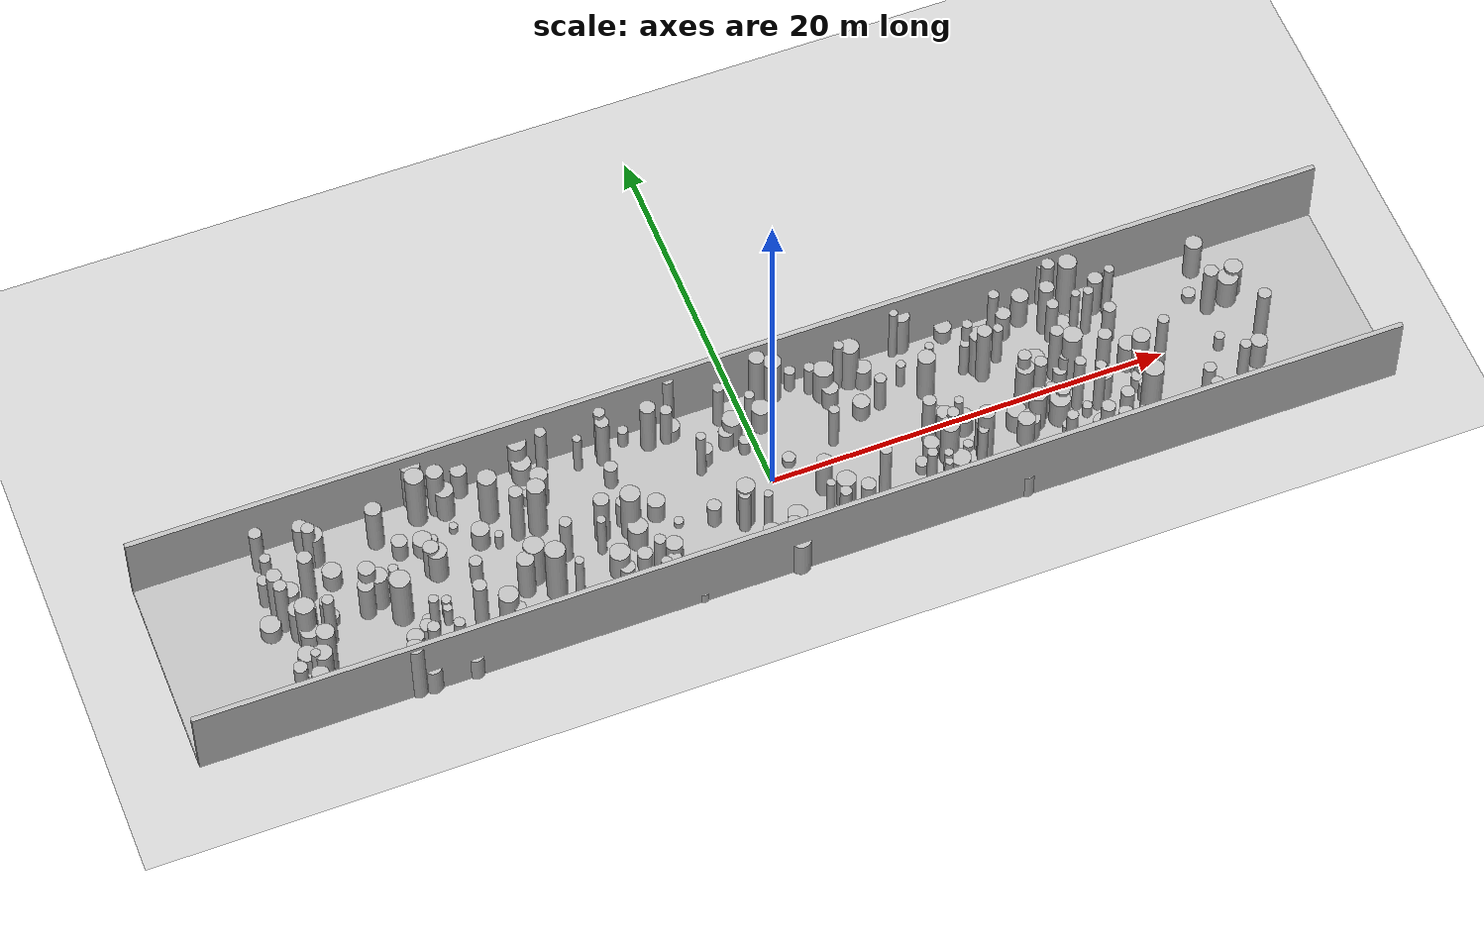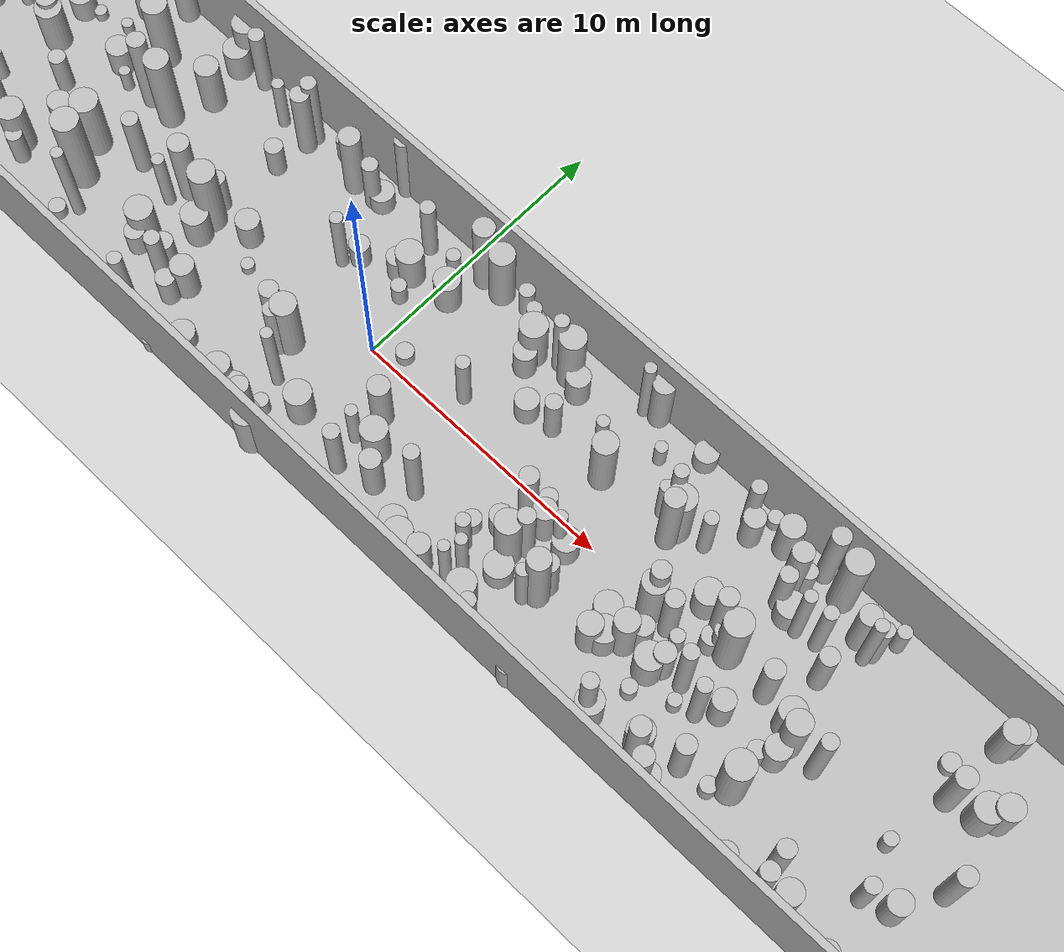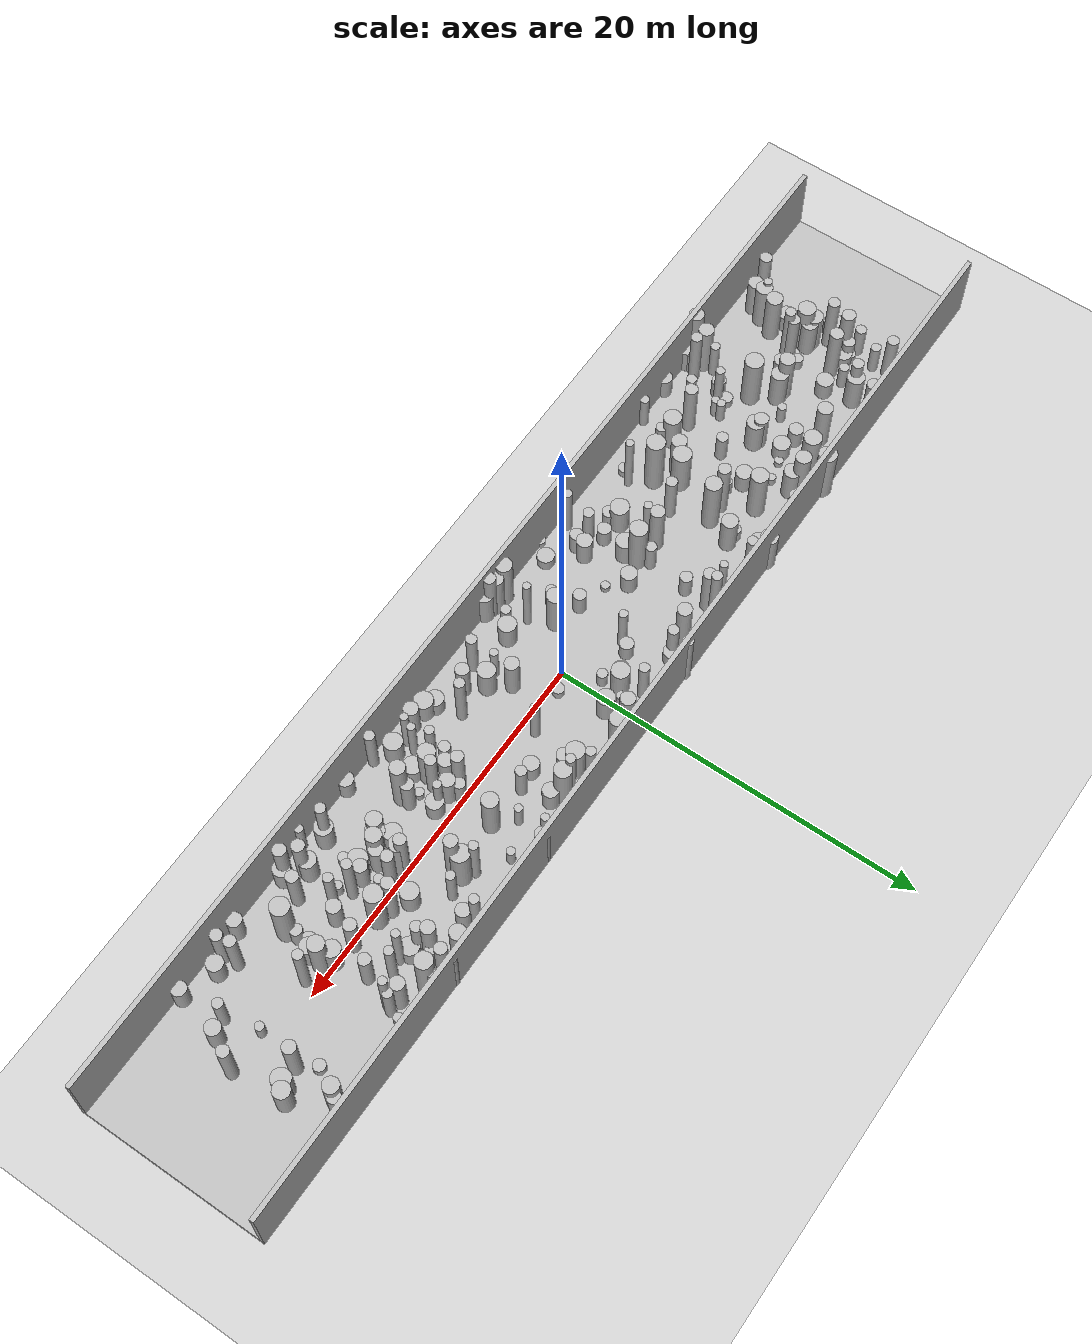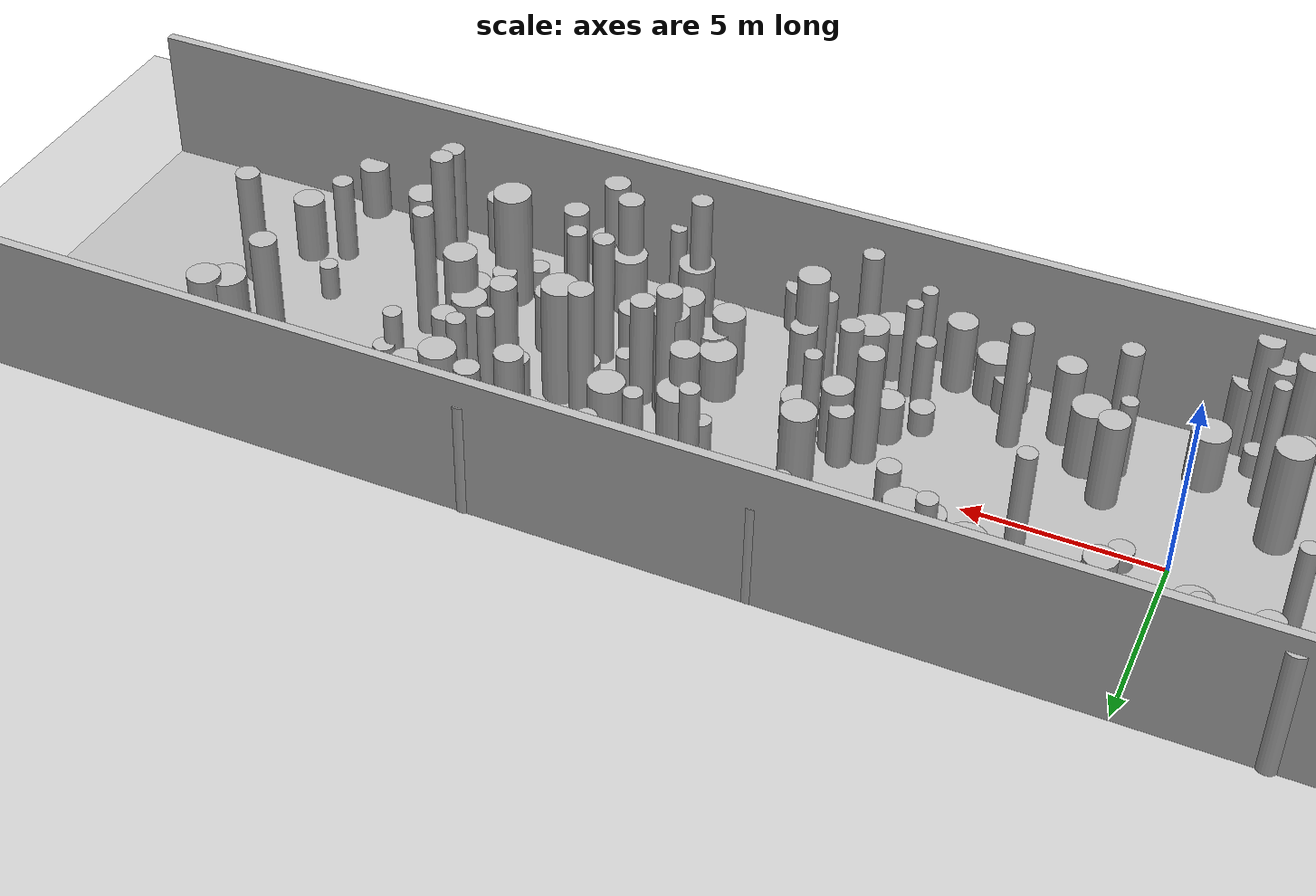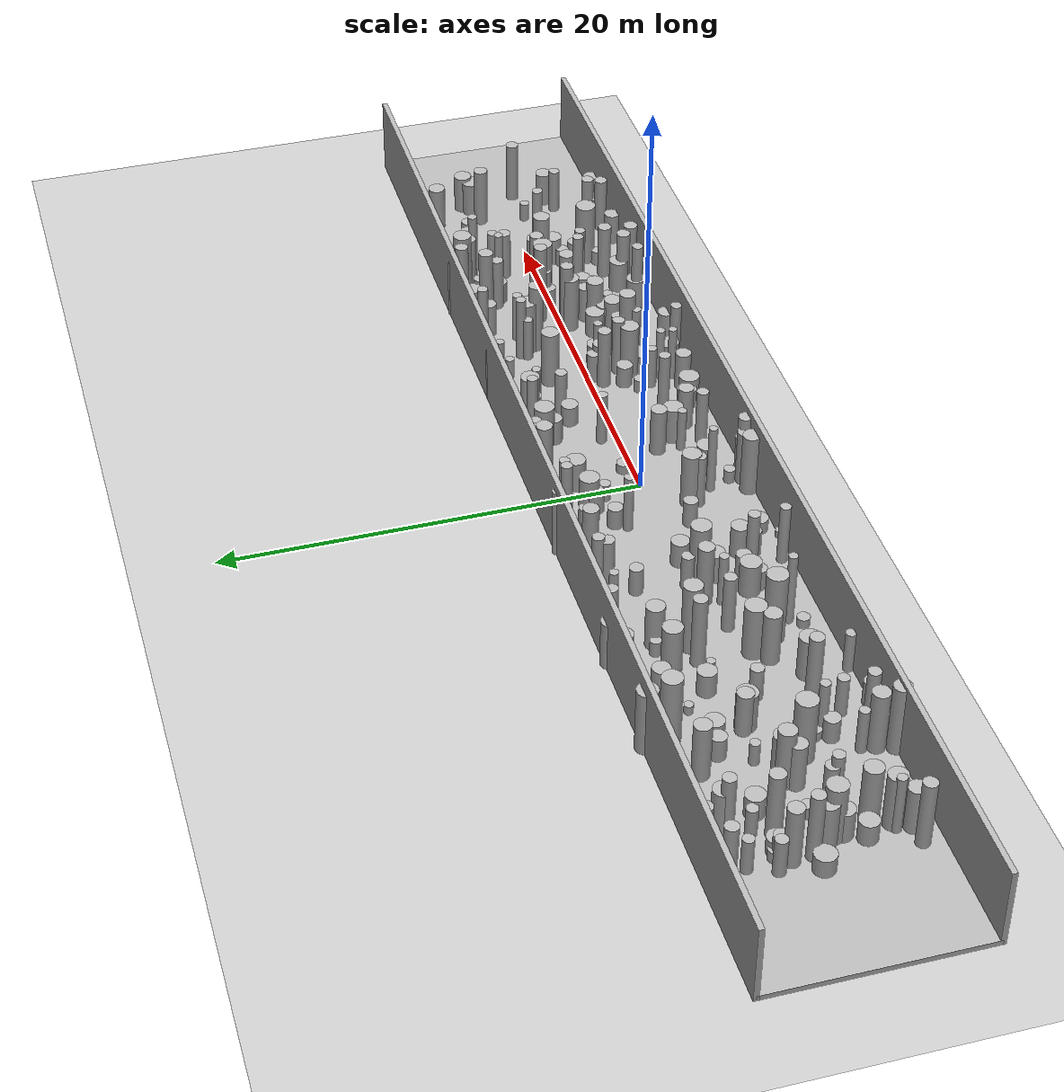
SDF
<?xml version="1.0"?>
<sdf version="1.4">
  <world name="default">
    <gui>
      <camera name="user_camera">
        <pose>-20 -30 40 0 0.66 0.83</pose>
      </camera>
    </gui>
    <include>
      <uri>model://ground_plane</uri>
    </include>
    <include>
      <uri>model://sun</uri>
    </include>
    <scene>
      <shadows>0</shadows>
    </scene>
    <model name="forest">
      <static>true</static>
      <link name="cylinder0">
        <pose>15.618833171189834 3.588085427933331 0.9756644041523093 0 0 0 </pose>
        <visual name="visual">
          <geometry>
            <cylinder>
              <radius>0.284359071309381</radius>
              <length>1.9513288083046185</length>
            </cylinder>
          </geometry>
        </visual>
        <collision name="collision">
          <geometry>
            <cylinder>
              <radius>0.284359071309381</radius>
              <length>1.9513288083046185</length>
            </cylinder>
          </geometry>
          <max_contacts>0</max_contacts>
        </collision>
      </link>
      <link name="cylinder1">
        <pose>-3.410056936858453 -1.2701892150677887 0.8086973027366486 0 0 0 </pose>
        <visual name="visual">
          <geometry>
            <cylinder>
              <radius>0.33904369996701267</radius>
              <length>1.6173946054732973</length>
            </cylinder>
          </geometry>
        </visual>
        <collision name="collision">
          <geometry>
            <cylinder>
              <radius>0.33904369996701267</radius>
              <length>1.6173946054732973</length>
            </cylinder>
          </geometry>
          <max_contacts>0</max_contacts>
        </collision>
      </link>
      <link name="cylinder2">
        <pose>15.869066007812819 2.5818272278221404 0.7011469668359454 0 0 0 </pose>
        <visual name="visual">
          <geometry>
            <cylinder>
              <radius>0.48590418580759787</radius>
              <length>1.4022939336718907</length>
            </cylinder>
          </geometry>
        </visual>
        <collision name="collision">
          <geometry>
            <cylinder>
              <radius>0.48590418580759787</radius>
              <length>1.4022939336718907</length>
            </cylinder>
          </geometry>
          <max_contacts>0</max_contacts>
        </collision>
      </link>
      <link name="cylinder3">
        <pose>1.6993842616417325 4.403585021799794 1.548561787785984 0 0 0 </pose>
        <visual name="visual">
          <geometry>
            <cylinder>
              <radius>0.44402708403622215</radius>
              <length>3.097123575571968</length>
            </cylinder>
          </geometry>
        </visual>
        <collision name="collision">
          <geometry>
            <cylinder>
              <radius>0.44402708403622215</radius>
              <length>3.097123575571968</length>
            </cylinder>
          </geometry>
          <max_contacts>0</max_contacts>
        </collision>
      </link>
      <link name="cylinder4">
        <pose>-3.6042722267468648 4.039614056958708 0.5409431707284422 0 0 0 </pose>
        <visual name="visual">
          <geometry>
            <cylinder>
              <radius>0.4456799034941059</radius>
              <length>1.0818863414568844</length>
            </cylinder>
          </geometry>
        </visual>
        <collision name="collision">
          <geometry>
            <cylinder>
              <radius>0.4456799034941059</radius>
              <length>1.0818863414568844</length>
            </cylinder>
          </geometry>
          <max_contacts>0</max_contacts>
        </collision>
      </link>
      <link name="cylinder5">
        <pose>-23.679742061325815 2.01241743389272 0.4087587626797539 0 0 0 </pose>
        <visual name="visual">
          <geometry>
            <cylinder>
              <radius>0.30006810378759863</radius>
              <length>0.8175175253595078</length>
            </cylinder>
          </geometry>
        </visual>
        <collision name="collision">
          <geometry>
            <cylinder>
              <radius>0.30006810378759863</radius>
              <length>0.8175175253595078</length>
            </cylinder>
          </geometry>
          <max_contacts>0</max_contacts>
        </collision>
      </link>
      <link name="cylinder6">
        <pose>18.455997076587373 3.163391686131545 1.880218039961245 0 0 0 </pose>
        <visual name="visual">
          <geometry>
            <cylinder>
              <radius>0.2290943265098593</radius>
              <length>3.76043607992249</length>
            </cylinder>
          </geometry>
        </visual>
        <collision name="collision">
          <geometry>
            <cylinder>
              <radius>0.2290943265098593</radius>
              <length>3.76043607992249</length>
            </cylinder>
          </geometry>
          <max_contacts>0</max_contacts>
        </collision>
      </link>
      <link name="cylinder7">
        <pose>-10.525573063987343 -0.618550906194625 1.607458766258477 0 0 0 </pose>
        <visual name="visual">
          <geometry>
            <cylinder>
              <radius>0.29693377543695243</radius>
              <length>3.214917532516954</length>
            </cylinder>
          </geometry>
        </visual>
        <collision name="collision">
          <geometry>
            <cylinder>
              <radius>0.29693377543695243</radius>
              <length>3.214917532516954</length>
            </cylinder>
          </geometry>
          <max_contacts>0</max_contacts>
        </collision>
      </link>
      <link name="cylinder8">
        <pose>-21.800550094250998 3.261826505791305 1.4079845272820526 0 0 0 </pose>
        <visual name="visual">
          <geometry>
            <cylinder>
              <radius>0.2014375265154011</radius>
              <length>2.815969054564105</length>
            </cylinder>
          </geometry>
        </visual>
        <collision name="collision">
          <geometry>
            <cylinder>
              <radius>0.2014375265154011</radius>
              <length>2.815969054564105</length>
            </cylinder>
          </geometry>
          <max_contacts>0</max_contacts>
        </collision>
      </link>
      <link name="cylinder9">
        <pose>-18.160809083049735 -4.134436356728669 1.8794305216573546 0 0 0 </pose>
        <visual name="visual">
          <geometry>
            <cylinder>
              <radius>0.2956200059763034</radius>
              <length>3.758861043314709</length>
            </cylinder>
          </geometry>
        </visual>
        <collision name="collision">
          <geometry>
            <cylinder>
              <radius>0.2956200059763034</radius>
              <length>3.758861043314709</length>
            </cylinder>
          </geometry>
          <max_contacts>0</max_contacts>
        </collision>
      </link>
      <link name="cylinder10">
        <pose>9.865297819089555 -1.9288175522242579 1.276608084734308 0 0 0 </pose>
        <visual name="visual">
          <geometry>
            <cylinder>
              <radius>0.3400789863354158</radius>
              <length>2.553216169468616</length>
            </cylinder>
          </geometry>
        </visual>
        <collision name="collision">
          <geometry>
            <cylinder>
              <radius>0.3400789863354158</radius>
              <length>2.553216169468616</length>
            </cylinder>
          </geometry>
          <max_contacts>0</max_contacts>
        </collision>
      </link>
      <link name="cylinder11">
        <pose>8.513826271152027 -1.5162641126023058 1.6599088720260913 0 0 0 </pose>
        <visual name="visual">
          <geometry>
            <cylinder>
              <radius>0.29402407786437507</radius>
              <length>3.3198177440521826</length>
            </cylinder>
          </geometry>
        </visual>
        <collision name="collision">
          <geometry>
            <cylinder>
              <radius>0.29402407786437507</radius>
              <length>3.3198177440521826</length>
            </cylinder>
          </geometry>
          <max_contacts>0</max_contacts>
        </collision>
      </link>
      <link name="cylinder12">
        <pose>24.150455095265748 1.7320600465595293 1.043892934087018 0 0 0 </pose>
        <visual name="visual">
          <geometry>
            <cylinder>
              <radius>0.4995793661794456</radius>
              <length>2.087785868174036</length>
            </cylinder>
          </geometry>
        </visual>
        <collision name="collision">
          <geometry>
            <cylinder>
              <radius>0.4995793661794456</radius>
              <length>2.087785868174036</length>
            </cylinder>
          </geometry>
          <max_contacts>0</max_contacts>
        </collision>
      </link>
      <link name="cylinder13">
        <pose>17.112769907476796 2.500177998868347 1.7635996860682448 0 0 0 </pose>
        <visual name="visual">
          <geometry>
            <cylinder>
              <radius>0.2428819846836711</radius>
              <length>3.5271993721364896</length>
            </cylinder>
          </geometry>
        </visual>
        <collision name="collision">
          <geometry>
            <cylinder>
              <radius>0.2428819846836711</radius>
              <length>3.5271993721364896</length>
            </cylinder>
          </geometry>
          <max_contacts>0</max_contacts>
        </collision>
      </link>
      <link name="cylinder14">
        <pose>9.075930163478006 -4.630681401572576 1.597628720508523 0 0 0 </pose>
        <visual name="visual">
          <geometry>
            <cylinder>
              <radius>0.2718848688338954</radius>
              <length>3.195257441017046</length>
            </cylinder>
          </geometry>
        </visual>
        <collision name="collision">
          <geometry>
            <cylinder>
              <radius>0.2718848688338954</radius>
              <length>3.195257441017046</length>
            </cylinder>
          </geometry>
          <max_contacts>0</max_contacts>
        </collision>
      </link>
      <link name="cylinder15">
        <pose>0.5785352989505945 2.9750292186021117 0.9102361143124422 0 0 0 </pose>
        <visual name="visual">
          <geometry>
            <cylinder>
              <radius>0.4637304822678691</radius>
              <length>1.8204722286248844</length>
            </cylinder>
          </geometry>
        </visual>
        <collision name="collision">
          <geometry>
            <cylinder>
              <radius>0.4637304822678691</radius>
              <length>1.8204722286248844</length>
            </cylinder>
          </geometry>
          <max_contacts>0</max_contacts>
        </collision>
      </link>
      <link name="cylinder16">
        <pose>-13.255122866712126 1.1187745779611848 0.6129788862393675 0 0 0 </pose>
        <visual name="visual">
          <geometry>
            <cylinder>
              <radius>0.20268167410298113</radius>
              <length>1.225957772478735</length>
            </cylinder>
          </geometry>
        </visual>
        <collision name="collision">
          <geometry>
            <cylinder>
              <radius>0.20268167410298113</radius>
              <length>1.225957772478735</length>
            </cylinder>
          </geometry>
          <max_contacts>0</max_contacts>
        </collision>
      </link>
      <link name="cylinder17">
        <pose>-4.775308046147366 3.8890800789210154 1.7092690073785224 0 0 0 </pose>
        <visual name="visual">
          <geometry>
            <cylinder>
              <radius>0.37615139349503185</radius>
              <length>3.4185380147570448</length>
            </cylinder>
          </geometry>
        </visual>
        <collision name="collision">
          <geometry>
            <cylinder>
              <radius>0.37615139349503185</radius>
              <length>3.4185380147570448</length>
            </cylinder>
          </geometry>
          <max_contacts>0</max_contacts>
        </collision>
      </link>
      <link name="cylinder18">
        <pose>-18.015127092285212 -2.5297718127896287 0.7112004149707867 0 0 0 </pose>
        <visual name="visual">
          <geometry>
            <cylinder>
              <radius>0.3739082902309111</radius>
              <length>1.4224008299415734</length>
            </cylinder>
          </geometry>
        </visual>
        <collision name="collision">
          <geometry>
            <cylinder>
              <radius>0.3739082902309111</radius>
              <length>1.4224008299415734</length>
            </cylinder>
          </geometry>
          <max_contacts>0</max_contacts>
        </collision>
      </link>
      <link name="cylinder19">
        <pose>-14.986373206738374 2.6608807107499732 0.34965633167286914 0 0 0 </pose>
        <visual name="visual">
          <geometry>
            <cylinder>
              <radius>0.20911420880428544</radius>
              <length>0.6993126633457383</length>
            </cylinder>
          </geometry>
        </visual>
        <collision name="collision">
          <geometry>
            <cylinder>
              <radius>0.20911420880428544</radius>
              <length>0.6993126633457383</length>
            </cylinder>
          </geometry>
          <max_contacts>0</max_contacts>
        </collision>
      </link>
      <link name="cylinder20">
        <pose>3.4435270528308592 0.8448754294673577 1.50543711050104 0 0 0 </pose>
        <visual name="visual">
          <geometry>
            <cylinder>
              <radius>0.2462129085398339</radius>
              <length>3.01087422100208</length>
            </cylinder>
          </geometry>
        </visual>
        <collision name="collision">
          <geometry>
            <cylinder>
              <radius>0.2462129085398339</radius>
              <length>3.01087422100208</length>
            </cylinder>
          </geometry>
          <max_contacts>0</max_contacts>
        </collision>
      </link>
      <link name="cylinder21">
        <pose>-0.7353567605645921 -4.716612959977095 1.8322252500576872 0 0 0 </pose>
        <visual name="visual">
          <geometry>
            <cylinder>
              <radius>0.32141102089215934</radius>
              <length>3.6644505001153744</length>
            </cylinder>
          </geometry>
        </visual>
        <collision name="collision">
          <geometry>
            <cylinder>
              <radius>0.32141102089215934</radius>
              <length>3.6644505001153744</length>
            </cylinder>
          </geometry>
          <max_contacts>0</max_contacts>
        </collision>
      </link>
      <link name="cylinder22">
        <pose>4.106205934701023 2.993755799769401 0.7927489453100149 0 0 0 </pose>
        <visual name="visual">
          <geometry>
            <cylinder>
              <radius>0.3991636697615998</radius>
              <length>1.5854978906200299</length>
            </cylinder>
          </geometry>
        </visual>
        <collision name="collision">
          <geometry>
            <cylinder>
              <radius>0.3991636697615998</radius>
              <length>1.5854978906200299</length>
            </cylinder>
          </geometry>
          <max_contacts>0</max_contacts>
        </collision>
      </link>
      <link name="cylinder23">
        <pose>-7.069070440820113 3.827537880866803 1.739081858629278 0 0 0 </pose>
        <visual name="visual">
          <geometry>
            <cylinder>
              <radius>0.3302921439886698</radius>
              <length>3.478163717258556</length>
            </cylinder>
          </geometry>
        </visual>
        <collision name="collision">
          <geometry>
            <cylinder>
              <radius>0.3302921439886698</radius>
              <length>3.478163717258556</length>
            </cylinder>
          </geometry>
          <max_contacts>0</max_contacts>
        </collision>
      </link>
      <link name="cylinder24">
        <pose>15.379908302124328 2.6982320132135733 1.5249028104789466 0 0 0 </pose>
        <visual name="visual">
          <geometry>
            <cylinder>
              <radius>0.29170336756379694</radius>
              <length>3.049805620957893</length>
            </cylinder>
          </geometry>
        </visual>
        <collision name="collision">
          <geometry>
            <cylinder>
              <radius>0.29170336756379694</radius>
              <length>3.049805620957893</length>
            </cylinder>
          </geometry>
          <max_contacts>0</max_contacts>
        </collision>
      </link>
      <link name="cylinder25">
        <pose>18.54262399304106 -1.115759782688095 0.8642403718463822 0 0 0 </pose>
        <visual name="visual">
          <geometry>
            <cylinder>
              <radius>0.4387119748478481</radius>
              <length>1.7284807436927645</length>
            </cylinder>
          </geometry>
        </visual>
        <collision name="collision">
          <geometry>
            <cylinder>
              <radius>0.4387119748478481</radius>
              <length>1.7284807436927645</length>
            </cylinder>
          </geometry>
          <max_contacts>0</max_contacts>
        </collision>
      </link>
      <link name="cylinder26">
        <pose>-15.441778785360121 -2.6818119872697443 1.7981005157965062 0 0 0 </pose>
        <visual name="visual">
          <geometry>
            <cylinder>
              <radius>0.33334163362651703</radius>
              <length>3.5962010315930124</length>
            </cylinder>
          </geometry>
        </visual>
        <collision name="collision">
          <geometry>
            <cylinder>
              <radius>0.33334163362651703</radius>
              <length>3.5962010315930124</length>
            </cylinder>
          </geometry>
          <max_contacts>0</max_contacts>
        </collision>
      </link>
      <link name="cylinder27">
        <pose>11.598955552039023 2.3641410631816733 1.506144262404247 0 0 0 </pose>
        <visual name="visual">
          <geometry>
            <cylinder>
              <radius>0.21004536015354663</radius>
              <length>3.012288524808494</length>
            </cylinder>
          </geometry>
        </visual>
        <collision name="collision">
          <geometry>
            <cylinder>
              <radius>0.21004536015354663</radius>
              <length>3.012288524808494</length>
            </cylinder>
          </geometry>
          <max_contacts>0</max_contacts>
        </collision>
      </link>
      <link name="cylinder28">
        <pose>19.636039116057468 -0.5828703103376895 1.9682462506496827 0 0 0 </pose>
        <visual name="visual">
          <geometry>
            <cylinder>
              <radius>0.270144772615278</radius>
              <length>3.9364925012993655</length>
            </cylinder>
          </geometry>
        </visual>
        <collision name="collision">
          <geometry>
            <cylinder>
              <radius>0.270144772615278</radius>
              <length>3.9364925012993655</length>
            </cylinder>
          </geometry>
          <max_contacts>0</max_contacts>
        </collision>
      </link>
      <link name="cylinder29">
        <pose>-0.9555137572657237 2.786083634189266 0.9702023812267938 0 0 0 </pose>
        <visual name="visual">
          <geometry>
            <cylinder>
              <radius>0.47938045877978486</radius>
              <length>1.9404047624535876</length>
            </cylinder>
          </geometry>
        </visual>
        <collision name="collision">
          <geometry>
            <cylinder>
              <radius>0.47938045877978486</radius>
              <length>1.9404047624535876</length>
            </cylinder>
          </geometry>
          <max_contacts>0</max_contacts>
        </collision>
      </link>
      <link name="cylinder30">
        <pose>23.082292544981804 1.5226431214101073 1.6966995700673215 0 0 0 </pose>
        <visual name="visual">
          <geometry>
            <cylinder>
              <radius>0.3513936600887434</radius>
              <length>3.393399140134643</length>
            </cylinder>
          </geometry>
        </visual>
        <collision name="collision">
          <geometry>
            <cylinder>
              <radius>0.3513936600887434</radius>
              <length>3.393399140134643</length>
            </cylinder>
          </geometry>
          <max_contacts>0</max_contacts>
        </collision>
      </link>
      <link name="cylinder31">
        <pose>-23.738585029574498 1.817528318224376 0.8247612334664344 0 0 0 </pose>
        <visual name="visual">
          <geometry>
            <cylinder>
              <radius>0.32685892989750714</radius>
              <length>1.6495224669328687</length>
            </cylinder>
          </geometry>
        </visual>
        <collision name="collision">
          <geometry>
            <cylinder>
              <radius>0.32685892989750714</radius>
              <length>1.6495224669328687</length>
            </cylinder>
          </geometry>
          <max_contacts>0</max_contacts>
        </collision>
      </link>
      <link name="cylinder32">
        <pose>15.814862429819492 4.413215667056303 1.937869286268463 0 0 0 </pose>
        <visual name="visual">
          <geometry>
            <cylinder>
              <radius>0.3162942934371233</radius>
              <length>3.875738572536926</length>
            </cylinder>
          </geometry>
        </visual>
        <collision name="collision">
          <geometry>
            <cylinder>
              <radius>0.3162942934371233</radius>
              <length>3.875738572536926</length>
            </cylinder>
          </geometry>
          <max_contacts>0</max_contacts>
        </collision>
      </link>
      <link name="cylinder33">
        <pose>-22.20371293826167 -1.0198286153366718 1.8924943667401357 0 0 0 </pose>
        <visual name="visual">
          <geometry>
            <cylinder>
              <radius>0.27601700017954345</radius>
              <length>3.7849887334802714</length>
            </cylinder>
          </geometry>
        </visual>
        <collision name="collision">
          <geometry>
            <cylinder>
              <radius>0.27601700017954345</radius>
              <length>3.7849887334802714</length>
            </cylinder>
          </geometry>
          <max_contacts>0</max_contacts>
        </collision>
      </link>
      <link name="cylinder34">
        <pose>20.73754939882896 -3.6138018554823095 1.7157958831736084 0 0 0 </pose>
        <visual name="visual">
          <geometry>
            <cylinder>
              <radius>0.30385086065369515</radius>
              <length>3.431591766347217</length>
            </cylinder>
          </geometry>
        </visual>
        <collision name="collision">
          <geometry>
            <cylinder>
              <radius>0.30385086065369515</radius>
              <length>3.431591766347217</length>
            </cylinder>
          </geometry>
          <max_contacts>0</max_contacts>
        </collision>
      </link>
      <link name="cylinder35">
        <pose>13.191856435925061 -1.275981524233222 1.0767416378343877 0 0 0 </pose>
        <visual name="visual">
          <geometry>
            <cylinder>
              <radius>0.3609251568033386</radius>
              <length>2.1534832756687754</length>
            </cylinder>
          </geometry>
        </visual>
        <collision name="collision">
          <geometry>
            <cylinder>
              <radius>0.3609251568033386</radius>
              <length>2.1534832756687754</length>
            </cylinder>
          </geometry>
          <max_contacts>0</max_contacts>
        </collision>
      </link>
      <link name="cylinder36">
        <pose>11.859981674240593 -1.3627390776222024 0.7691769947685593 0 0 0 </pose>
        <visual name="visual">
          <geometry>
            <cylinder>
              <radius>0.46901480650192656</radius>
              <length>1.5383539895371185</length>
            </cylinder>
          </geometry>
        </visual>
        <collision name="collision">
          <geometry>
            <cylinder>
              <radius>0.46901480650192656</radius>
              <length>1.5383539895371185</length>
            </cylinder>
          </geometry>
          <max_contacts>0</max_contacts>
        </collision>
      </link>
      <link name="cylinder37">
        <pose>16.276966125051594 -4.434674739766317 0.8388820520679676 0 0 0 </pose>
        <visual name="visual">
          <geometry>
            <cylinder>
              <radius>0.44120714200989547</radius>
              <length>1.6777641041359352</length>
            </cylinder>
          </geometry>
        </visual>
        <collision name="collision">
          <geometry>
            <cylinder>
              <radius>0.44120714200989547</radius>
              <length>1.6777641041359352</length>
            </cylinder>
          </geometry>
          <max_contacts>0</max_contacts>
        </collision>
      </link>
      <link name="cylinder38">
        <pose>7.666241506215989 2.8532443910162995 0.9271853040387164 0 0 0 </pose>
        <visual name="visual">
          <geometry>
            <cylinder>
              <radius>0.21847830880316244</radius>
              <length>1.8543706080774327</length>
            </cylinder>
          </geometry>
        </visual>
        <collision name="collision">
          <geometry>
            <cylinder>
              <radius>0.21847830880316244</radius>
              <length>1.8543706080774327</length>
            </cylinder>
          </geometry>
          <max_contacts>0</max_contacts>
        </collision>
      </link>
      <link name="cylinder39">
        <pose>23.255342255212724 3.8501029476427124 1.3054705178780175 0 0 0 </pose>
        <visual name="visual">
          <geometry>
            <cylinder>
              <radius>0.41637683367174433</radius>
              <length>2.610941035756035</length>
            </cylinder>
          </geometry>
        </visual>
        <collision name="collision">
          <geometry>
            <cylinder>
              <radius>0.41637683367174433</radius>
              <length>2.610941035756035</length>
            </cylinder>
          </geometry>
          <max_contacts>0</max_contacts>
        </collision>
      </link>
      <link name="cylinder40">
        <pose>-18.49357560465792 1.0151491741998022 0.7010873580335185 0 0 0 </pose>
        <visual name="visual">
          <geometry>
            <cylinder>
              <radius>0.23333337634097945</radius>
              <length>1.402174716067037</length>
            </cylinder>
          </geometry>
        </visual>
        <collision name="collision">
          <geometry>
            <cylinder>
              <radius>0.23333337634097945</radius>
              <length>1.402174716067037</length>
            </cylinder>
          </geometry>
          <max_contacts>0</max_contacts>
        </collision>
      </link>
      <link name="cylinder41">
        <pose>-16.223117321788628 4.930585165584869 1.644054146244402 0 0 0 </pose>
        <visual name="visual">
          <geometry>
            <cylinder>
              <radius>0.48408230626222676</radius>
              <length>3.288108292488804</length>
            </cylinder>
          </geometry>
        </visual>
        <collision name="collision">
          <geometry>
            <cylinder>
              <radius>0.48408230626222676</radius>
              <length>3.288108292488804</length>
            </cylinder>
          </geometry>
          <max_contacts>0</max_contacts>
        </collision>
      </link>
      <link name="cylinder42">
        <pose>-8.307093750710266 -2.8164997007199197 0.6622072614163566 0 0 0 </pose>
        <visual name="visual">
          <geometry>
            <cylinder>
              <radius>0.35939469345647124</radius>
              <length>1.324414522832713</length>
            </cylinder>
          </geometry>
        </visual>
        <collision name="collision">
          <geometry>
            <cylinder>
              <radius>0.35939469345647124</radius>
              <length>1.324414522832713</length>
            </cylinder>
          </geometry>
          <max_contacts>0</max_contacts>
        </collision>
      </link>
      <link name="cylinder43">
        <pose>-21.837048398225804 -0.08602022806299559 0.43983961650292613 0 0 0 </pose>
        <visual name="visual">
          <geometry>
            <cylinder>
              <radius>0.31036477772576027</radius>
              <length>0.8796792330058523</length>
            </cylinder>
          </geometry>
        </visual>
        <collision name="collision">
          <geometry>
            <cylinder>
              <radius>0.31036477772576027</radius>
              <length>0.8796792330058523</length>
            </cylinder>
          </geometry>
          <max_contacts>0</max_contacts>
        </collision>
      </link>
      <link name="cylinder44">
        <pose>0.904040064140414 4.390043288172659 1.9281252989354605 0 0 0 </pose>
        <visual name="visual">
          <geometry>
            <cylinder>
              <radius>0.3819991879143706</radius>
              <length>3.856250597870921</length>
            </cylinder>
          </geometry>
        </visual>
        <collision name="collision">
          <geometry>
            <cylinder>
              <radius>0.3819991879143706</radius>
              <length>3.856250597870921</length>
            </cylinder>
          </geometry>
          <max_contacts>0</max_contacts>
        </collision>
      </link>
      <link name="cylinder45">
        <pose>13.994288956120911 -2.66267086356186 0.4747905248318759 0 0 0 </pose>
        <visual name="visual">
          <geometry>
            <cylinder>
              <radius>0.2674987229767347</radius>
              <length>0.9495810496637518</length>
            </cylinder>
          </geometry>
        </visual>
        <collision name="collision">
          <geometry>
            <cylinder>
              <radius>0.2674987229767347</radius>
              <length>0.9495810496637518</length>
            </cylinder>
          </geometry>
          <max_contacts>0</max_contacts>
        </collision>
      </link>
      <link name="cylinder46">
        <pose>-12.891575511027565 -1.708502826013473 1.4711535961352924 0 0 0 </pose>
        <visual name="visual">
          <geometry>
            <cylinder>
              <radius>0.4126154002610912</radius>
              <length>2.942307192270585</length>
            </cylinder>
          </geometry>
        </visual>
        <collision name="collision">
          <geometry>
            <cylinder>
              <radius>0.4126154002610912</radius>
              <length>2.942307192270585</length>
            </cylinder>
          </geometry>
          <max_contacts>0</max_contacts>
        </collision>
      </link>
      <link name="cylinder47">
        <pose>18.57813850079186 3.4514887648950925 1.4668577012974344 0 0 0 </pose>
        <visual name="visual">
          <geometry>
            <cylinder>
              <radius>0.26758956376388604</radius>
              <length>2.933715402594869</length>
            </cylinder>
          </geometry>
        </visual>
        <collision name="collision">
          <geometry>
            <cylinder>
              <radius>0.26758956376388604</radius>
              <length>2.933715402594869</length>
            </cylinder>
          </geometry>
          <max_contacts>0</max_contacts>
        </collision>
      </link>
      <link name="cylinder48">
        <pose>24.03937666618416 -2.1780653879687817 1.0182782667376573 0 0 0 </pose>
        <visual name="visual">
          <geometry>
            <cylinder>
              <radius>0.4089840134096435</radius>
              <length>2.0365565334753146</length>
            </cylinder>
          </geometry>
        </visual>
        <collision name="collision">
          <geometry>
            <cylinder>
              <radius>0.4089840134096435</radius>
              <length>2.0365565334753146</length>
            </cylinder>
          </geometry>
          <max_contacts>0</max_contacts>
        </collision>
      </link>
      <link name="cylinder49">
        <pose>7.953252640835039 4.574869728848338 1.8128917431856637 0 0 0 </pose>
        <visual name="visual">
          <geometry>
            <cylinder>
              <radius>0.2049968974062898</radius>
              <length>3.6257834863713274</length>
            </cylinder>
          </geometry>
        </visual>
        <collision name="collision">
          <geometry>
            <cylinder>
              <radius>0.2049968974062898</radius>
              <length>3.6257834863713274</length>
            </cylinder>
          </geometry>
          <max_contacts>0</max_contacts>
        </collision>
      </link>
      <link name="cylinder50">
        <pose>15.269410494350545 -2.0173740347192215 0.5005023824854737 0 0 0 </pose>
        <visual name="visual">
          <geometry>
            <cylinder>
              <radius>0.23815286945406217</radius>
              <length>1.0010047649709475</length>
            </cylinder>
          </geometry>
        </visual>
        <collision name="collision">
          <geometry>
            <cylinder>
              <radius>0.23815286945406217</radius>
              <length>1.0010047649709475</length>
            </cylinder>
          </geometry>
          <max_contacts>0</max_contacts>
        </collision>
      </link>
      <link name="cylinder51">
        <pose>4.672101008395934 -2.6002466242280886 1.8634355950134864 0 0 0 </pose>
        <visual name="visual">
          <geometry>
            <cylinder>
              <radius>0.27376685721473126</radius>
              <length>3.726871190026973</length>
            </cylinder>
          </geometry>
        </visual>
        <collision name="collision">
          <geometry>
            <cylinder>
              <radius>0.27376685721473126</radius>
              <length>3.726871190026973</length>
            </cylinder>
          </geometry>
          <max_contacts>0</max_contacts>
        </collision>
      </link>
      <link name="cylinder52">
        <pose>-16.8601363615864 -2.0002097697674657 0.7412490017964124 0 0 0 </pose>
        <visual name="visual">
          <geometry>
            <cylinder>
              <radius>0.2123701967409388</radius>
              <length>1.4824980035928248</length>
            </cylinder>
          </geometry>
        </visual>
        <collision name="collision">
          <geometry>
            <cylinder>
              <radius>0.2123701967409388</radius>
              <length>1.4824980035928248</length>
            </cylinder>
          </geometry>
          <max_contacts>0</max_contacts>
        </collision>
      </link>
      <link name="cylinder53">
        <pose>-13.144577644127398 2.8485634309416943 1.7484170588877241 0 0 0 </pose>
        <visual name="visual">
          <geometry>
            <cylinder>
              <radius>0.45996686888993416</radius>
              <length>3.4968341177754483</length>
            </cylinder>
          </geometry>
        </visual>
        <collision name="collision">
          <geometry>
            <cylinder>
              <radius>0.45996686888993416</radius>
              <length>3.4968341177754483</length>
            </cylinder>
          </geometry>
          <max_contacts>0</max_contacts>
        </collision>
      </link>
      <link name="cylinder54">
        <pose>15.012602676140695 -1.3892620521165688 1.9798684967381748 0 0 0 </pose>
        <visual name="visual">
          <geometry>
            <cylinder>
              <radius>0.2675338532130522</radius>
              <length>3.9597369934763496</length>
            </cylinder>
          </geometry>
        </visual>
        <collision name="collision">
          <geometry>
            <cylinder>
              <radius>0.2675338532130522</radius>
              <length>3.9597369934763496</length>
            </cylinder>
          </geometry>
          <max_contacts>0</max_contacts>
        </collision>
      </link>
      <link name="cylinder55">
        <pose>-8.5950041946599 -0.18264373152601188 1.7082149559520043 0 0 0 </pose>
        <visual name="visual">
          <geometry>
            <cylinder>
              <radius>0.37351376677049514</radius>
              <length>3.4164299119040087</length>
            </cylinder>
          </geometry>
        </visual>
        <collision name="collision">
          <geometry>
            <cylinder>
              <radius>0.37351376677049514</radius>
              <length>3.4164299119040087</length>
            </cylinder>
          </geometry>
          <max_contacts>0</max_contacts>
        </collision>
      </link>
      <link name="cylinder56">
        <pose>-5.861789615702062 4.453023283589221 0.6557879777366558 0 0 0 </pose>
        <visual name="visual">
          <geometry>
            <cylinder>
              <radius>0.25591483969236617</radius>
              <length>1.3115759554733115</length>
            </cylinder>
          </geometry>
        </visual>
        <collision name="collision">
          <geometry>
            <cylinder>
              <radius>0.25591483969236617</radius>
              <length>1.3115759554733115</length>
            </cylinder>
          </geometry>
          <max_contacts>0</max_contacts>
        </collision>
      </link>
      <link name="cylinder57">
        <pose>-1.216583282131932 3.942091139612856 1.5413353604361941 0 0 0 </pose>
        <visual name="visual">
          <geometry>
            <cylinder>
              <radius>0.2659817680177529</radius>
              <length>3.0826707208723882</length>
            </cylinder>
          </geometry>
        </visual>
        <collision name="collision">
          <geometry>
            <cylinder>
              <radius>0.2659817680177529</radius>
              <length>3.0826707208723882</length>
            </cylinder>
          </geometry>
          <max_contacts>0</max_contacts>
        </collision>
      </link>
      <link name="cylinder58">
        <pose>-11.255020018472834 1.3289213521882672 1.9238639992878968 0 0 0 </pose>
        <visual name="visual">
          <geometry>
            <cylinder>
              <radius>0.4449356155917538</radius>
              <length>3.8477279985757935</length>
            </cylinder>
          </geometry>
        </visual>
        <collision name="collision">
          <geometry>
            <cylinder>
              <radius>0.4449356155917538</radius>
              <length>3.8477279985757935</length>
            </cylinder>
          </geometry>
          <max_contacts>0</max_contacts>
        </collision>
      </link>
      <link name="cylinder59">
        <pose>-24.002782389595684 0.5042752308654723 1.8770728420283596 0 0 0 </pose>
        <visual name="visual">
          <geometry>
            <cylinder>
              <radius>0.3143003682034119</radius>
              <length>3.754145684056719</length>
            </cylinder>
          </geometry>
        </visual>
        <collision name="collision">
          <geometry>
            <cylinder>
              <radius>0.3143003682034119</radius>
              <length>3.754145684056719</length>
            </cylinder>
          </geometry>
          <max_contacts>0</max_contacts>
        </collision>
      </link>
      <link name="cylinder60">
        <pose>-11.20258796285028 -3.8493136906173753 0.3564758136327316 0 0 0 </pose>
        <visual name="visual">
          <geometry>
            <cylinder>
              <radius>0.2998729793484964</radius>
              <length>0.7129516272654632</length>
            </cylinder>
          </geometry>
        </visual>
        <collision name="collision">
          <geometry>
            <cylinder>
              <radius>0.2998729793484964</radius>
              <length>0.7129516272654632</length>
            </cylinder>
          </geometry>
          <max_contacts>0</max_contacts>
        </collision>
      </link>
      <link name="cylinder61">
        <pose>16.672888331410277 -3.309221816926564 1.5698820206153767 0 0 0 </pose>
        <visual name="visual">
          <geometry>
            <cylinder>
              <radius>0.32848772290761613</radius>
              <length>3.1397640412307535</length>
            </cylinder>
          </geometry>
        </visual>
        <collision name="collision">
          <geometry>
            <cylinder>
              <radius>0.32848772290761613</radius>
              <length>3.1397640412307535</length>
            </cylinder>
          </geometry>
          <max_contacts>0</max_contacts>
        </collision>
      </link>
      <link name="cylinder62">
        <pose>5.987886354903342 3.5073927301963845 0.8142929368390077 0 0 0 </pose>
        <visual name="visual">
          <geometry>
            <cylinder>
              <radius>0.4178552959836793</radius>
              <length>1.6285858736780154</length>
            </cylinder>
          </geometry>
        </visual>
        <collision name="collision">
          <geometry>
            <cylinder>
              <radius>0.4178552959836793</radius>
              <length>1.6285858736780154</length>
            </cylinder>
          </geometry>
          <max_contacts>0</max_contacts>
        </collision>
      </link>
      <link name="cylinder63">
        <pose>8.476384591417855 -2.7030263662355027 0.5978973282370059 0 0 0 </pose>
        <visual name="visual">
          <geometry>
            <cylinder>
              <radius>0.4971026707762667</radius>
              <length>1.1957946564740118</length>
            </cylinder>
          </geometry>
        </visual>
        <collision name="collision">
          <geometry>
            <cylinder>
              <radius>0.4971026707762667</radius>
              <length>1.1957946564740118</length>
            </cylinder>
          </geometry>
          <max_contacts>0</max_contacts>
        </collision>
      </link>
      <link name="cylinder64">
        <pose>2.7619240202183164 -2.455753605274219 1.0691079849985297 0 0 0 </pose>
        <visual name="visual">
          <geometry>
            <cylinder>
              <radius>0.47196936832046193</radius>
              <length>2.1382159699970593</length>
            </cylinder>
          </geometry>
        </visual>
        <collision name="collision">
          <geometry>
            <cylinder>
              <radius>0.47196936832046193</radius>
              <length>2.1382159699970593</length>
            </cylinder>
          </geometry>
          <max_contacts>0</max_contacts>
        </collision>
      </link>
      <link name="cylinder65">
        <pose>5.555162849658647 -4.183981940254874 0.7771060286569154 0 0 0 </pose>
        <visual name="visual">
          <geometry>
            <cylinder>
              <radius>0.4940623162058991</radius>
              <length>1.5542120573138307</length>
            </cylinder>
          </geometry>
        </visual>
        <collision name="collision">
          <geometry>
            <cylinder>
              <radius>0.4940623162058991</radius>
              <length>1.5542120573138307</length>
            </cylinder>
          </geometry>
          <max_contacts>0</max_contacts>
        </collision>
      </link>
      <link name="cylinder66">
        <pose>-14.1715463676721 -2.917855704786513 1.2150279252211407 0 0 0 </pose>
        <visual name="visual">
          <geometry>
            <cylinder>
              <radius>0.47778043909406503</radius>
              <length>2.4300558504422813</length>
            </cylinder>
          </geometry>
        </visual>
        <collision name="collision">
          <geometry>
            <cylinder>
              <radius>0.47778043909406503</radius>
              <length>2.4300558504422813</length>
            </cylinder>
          </geometry>
          <max_contacts>0</max_contacts>
        </collision>
      </link>
      <link name="cylinder67">
        <pose>15.37684174129182 0.35065000647642375 1.8094163151189908 0 0 0 </pose>
        <visual name="visual">
          <geometry>
            <cylinder>
              <radius>0.48074946533755103</radius>
              <length>3.6188326302379816</length>
            </cylinder>
          </geometry>
        </visual>
        <collision name="collision">
          <geometry>
            <cylinder>
              <radius>0.48074946533755103</radius>
              <length>3.6188326302379816</length>
            </cylinder>
          </geometry>
          <max_contacts>0</max_contacts>
        </collision>
      </link>
      <link name="cylinder68">
        <pose>-14.887149694921693 -0.34536853120764555 0.9706076712247758 0 0 0 </pose>
        <visual name="visual">
          <geometry>
            <cylinder>
              <radius>0.30774516073615427</radius>
              <length>1.9412153424495515</length>
            </cylinder>
          </geometry>
        </visual>
        <collision name="collision">
          <geometry>
            <cylinder>
              <radius>0.30774516073615427</radius>
              <length>1.9412153424495515</length>
            </cylinder>
          </geometry>
          <max_contacts>0</max_contacts>
        </collision>
      </link>
      <link name="cylinder69">
        <pose>18.58042648452023 -0.5070248052006363 1.524559431131524 0 0 0 </pose>
        <visual name="visual">
          <geometry>
            <cylinder>
              <radius>0.4281576148169088</radius>
              <length>3.049118862263048</length>
            </cylinder>
          </geometry>
        </visual>
        <collision name="collision">
          <geometry>
            <cylinder>
              <radius>0.4281576148169088</radius>
              <length>3.049118862263048</length>
            </cylinder>
          </geometry>
          <max_contacts>0</max_contacts>
        </collision>
      </link>
      <link name="cylinder70">
        <pose>-16.792238933854627 -1.6147479718565183 0.7901780546410666 0 0 0 </pose>
        <visual name="visual">
          <geometry>
            <cylinder>
              <radius>0.23072785165468096</radius>
              <length>1.5803561092821332</length>
            </cylinder>
          </geometry>
        </visual>
        <collision name="collision">
          <geometry>
            <cylinder>
              <radius>0.23072785165468096</radius>
              <length>1.5803561092821332</length>
            </cylinder>
          </geometry>
          <max_contacts>0</max_contacts>
        </collision>
      </link>
      <link name="cylinder71">
        <pose>15.930446132314394 -1.773278490948742 1.8377988796069769 0 0 0 </pose>
        <visual name="visual">
          <geometry>
            <cylinder>
              <radius>0.2559288661274516</radius>
              <length>3.6755977592139537</length>
            </cylinder>
          </geometry>
        </visual>
        <collision name="collision">
          <geometry>
            <cylinder>
              <radius>0.2559288661274516</radius>
              <length>3.6755977592139537</length>
            </cylinder>
          </geometry>
          <max_contacts>0</max_contacts>
        </collision>
      </link>
      <link name="cylinder72">
        <pose>-8.315024353677362 3.9044192635447157 1.3431335159264037 0 0 0 </pose>
        <visual name="visual">
          <geometry>
            <cylinder>
              <radius>0.2103194928219873</radius>
              <length>2.6862670318528075</length>
            </cylinder>
          </geometry>
        </visual>
        <collision name="collision">
          <geometry>
            <cylinder>
              <radius>0.2103194928219873</radius>
              <length>2.6862670318528075</length>
            </cylinder>
          </geometry>
          <max_contacts>0</max_contacts>
        </collision>
      </link>
      <link name="cylinder73">
        <pose>22.6674340597403 -0.745565272382672 0.6230078139268471 0 0 0 </pose>
        <visual name="visual">
          <geometry>
            <cylinder>
              <radius>0.24237221904012846</radius>
              <length>1.2460156278536942</length>
            </cylinder>
          </geometry>
        </visual>
        <collision name="collision">
          <geometry>
            <cylinder>
              <radius>0.24237221904012846</radius>
              <length>1.2460156278536942</length>
            </cylinder>
          </geometry>
          <max_contacts>0</max_contacts>
        </collision>
      </link>
      <link name="cylinder74">
        <pose>-5.344949083121492 -4.9527701439744884 0.3000630937218423 0 0 0 </pose>
        <visual name="visual">
          <geometry>
            <cylinder>
              <radius>0.2527022216960019</radius>
              <length>0.6001261874436846</length>
            </cylinder>
          </geometry>
        </visual>
        <collision name="collision">
          <geometry>
            <cylinder>
              <radius>0.2527022216960019</radius>
              <length>0.6001261874436846</length>
            </cylinder>
          </geometry>
          <max_contacts>0</max_contacts>
        </collision>
      </link>
      <link name="cylinder75">
        <pose>17.894258685637396 1.6676075241893713 1.4346094551642614 0 0 0 </pose>
        <visual name="visual">
          <geometry>
            <cylinder>
              <radius>0.3206421124256456</radius>
              <length>2.869218910328523</length>
            </cylinder>
          </geometry>
        </visual>
        <collision name="collision">
          <geometry>
            <cylinder>
              <radius>0.3206421124256456</radius>
              <length>2.869218910328523</length>
            </cylinder>
          </geometry>
          <max_contacts>0</max_contacts>
        </collision>
      </link>
      <link name="cylinder76">
        <pose>-23.21263782120473 -3.178663896762618 1.5342078549653122 0 0 0 </pose>
        <visual name="visual">
          <geometry>
            <cylinder>
              <radius>0.441936661298123</radius>
              <length>3.0684157099306244</length>
            </cylinder>
          </geometry>
        </visual>
        <collision name="collision">
          <geometry>
            <cylinder>
              <radius>0.441936661298123</radius>
              <length>3.0684157099306244</length>
            </cylinder>
          </geometry>
          <max_contacts>0</max_contacts>
        </collision>
      </link>
      <link name="cylinder77">
        <pose>-16.689673175686437 2.135176522671366 0.6310616914309508 0 0 0 </pose>
        <visual name="visual">
          <geometry>
            <cylinder>
              <radius>0.45890008550078465</radius>
              <length>1.2621233828619016</length>
            </cylinder>
          </geometry>
        </visual>
        <collision name="collision">
          <geometry>
            <cylinder>
              <radius>0.45890008550078465</radius>
              <length>1.2621233828619016</length>
            </cylinder>
          </geometry>
          <max_contacts>0</max_contacts>
        </collision>
      </link>
      <link name="cylinder78">
        <pose>-0.48821396889628943 -4.9151921007384605 1.127450024972422 0 0 0 </pose>
        <visual name="visual">
          <geometry>
            <cylinder>
              <radius>0.48897684717883183</radius>
              <length>2.254900049944844</length>
            </cylinder>
          </geometry>
        </visual>
        <collision name="collision">
          <geometry>
            <cylinder>
              <radius>0.48897684717883183</radius>
              <length>2.254900049944844</length>
            </cylinder>
          </geometry>
          <max_contacts>0</max_contacts>
        </collision>
      </link>
      <link name="cylinder79">
        <pose>-10.999800799312503 4.311692076800821 0.7698859985121229 0 0 0 </pose>
        <visual name="visual">
          <geometry>
            <cylinder>
              <radius>0.4735187933917541</radius>
              <length>1.5397719970242458</length>
            </cylinder>
          </geometry>
        </visual>
        <collision name="collision">
          <geometry>
            <cylinder>
              <radius>0.4735187933917541</radius>
              <length>1.5397719970242458</length>
            </cylinder>
          </geometry>
          <max_contacts>0</max_contacts>
        </collision>
      </link>
      <link name="cylinder80">
        <pose>18.188932230299365 -2.131682857904363 0.7354274663817877 0 0 0 </pose>
        <visual name="visual">
          <geometry>
            <cylinder>
              <radius>0.31975378407033034</radius>
              <length>1.4708549327635754</length>
            </cylinder>
          </geometry>
        </visual>
        <collision name="collision">
          <geometry>
            <cylinder>
              <radius>0.31975378407033034</radius>
              <length>1.4708549327635754</length>
            </cylinder>
          </geometry>
          <max_contacts>0</max_contacts>
        </collision>
      </link>
      <link name="cylinder81">
        <pose>-20.1601837393649 -0.1788693429490804 1.3222436946086389 0 0 0 </pose>
        <visual name="visual">
          <geometry>
            <cylinder>
              <radius>0.39195667636804743</radius>
              <length>2.6444873892172778</length>
            </cylinder>
          </geometry>
        </visual>
        <collision name="collision">
          <geometry>
            <cylinder>
              <radius>0.39195667636804743</radius>
              <length>2.6444873892172778</length>
            </cylinder>
          </geometry>
          <max_contacts>0</max_contacts>
        </collision>
      </link>
      <link name="cylinder82">
        <pose>1.9240226608488058 -2.603008552193422 1.2350960365866193 0 0 0 </pose>
        <visual name="visual">
          <geometry>
            <cylinder>
              <radius>0.2125009094644301</radius>
              <length>2.4701920731732385</length>
            </cylinder>
          </geometry>
        </visual>
        <collision name="collision">
          <geometry>
            <cylinder>
              <radius>0.2125009094644301</radius>
              <length>2.4701920731732385</length>
            </cylinder>
          </geometry>
          <max_contacts>0</max_contacts>
        </collision>
      </link>
      <link name="cylinder83">
        <pose>-19.315599351364842 -4.890521053171561 1.9078571329891796 0 0 0 </pose>
        <visual name="visual">
          <geometry>
            <cylinder>
              <radius>0.40758707059049837</radius>
              <length>3.815714265978359</length>
            </cylinder>
          </geometry>
        </visual>
        <collision name="collision">
          <geometry>
            <cylinder>
              <radius>0.40758707059049837</radius>
              <length>3.815714265978359</length>
            </cylinder>
          </geometry>
          <max_contacts>0</max_contacts>
        </collision>
      </link>
      <link name="cylinder84">
        <pose>-3.3835551550107823 4.963984115556979 1.7615465854213015 0 0 0 </pose>
        <visual name="visual">
          <geometry>
            <cylinder>
              <radius>0.285282159561505</radius>
              <length>3.523093170842603</length>
            </cylinder>
          </geometry>
        </visual>
        <collision name="collision">
          <geometry>
            <cylinder>
              <radius>0.285282159561505</radius>
              <length>3.523093170842603</length>
            </cylinder>
          </geometry>
          <max_contacts>0</max_contacts>
        </collision>
      </link>
      <link name="cylinder85">
        <pose>-19.047170470343634 -4.106897316308888 1.7123463860957733 0 0 0 </pose>
        <visual name="visual">
          <geometry>
            <cylinder>
              <radius>0.40598088709907587</radius>
              <length>3.4246927721915466</length>
            </cylinder>
          </geometry>
        </visual>
        <collision name="collision">
          <geometry>
            <cylinder>
              <radius>0.40598088709907587</radius>
              <length>3.4246927721915466</length>
            </cylinder>
          </geometry>
          <max_contacts>0</max_contacts>
        </collision>
      </link>
      <link name="cylinder86">
        <pose>-17.565739772354643 -2.2725960441776794 1.518001080866863 0 0 0 </pose>
        <visual name="visual">
          <geometry>
            <cylinder>
              <radius>0.2343963553725524</radius>
              <length>3.036002161733726</length>
            </cylinder>
          </geometry>
        </visual>
        <collision name="collision">
          <geometry>
            <cylinder>
              <radius>0.2343963553725524</radius>
              <length>3.036002161733726</length>
            </cylinder>
          </geometry>
          <max_contacts>0</max_contacts>
        </collision>
      </link>
      <link name="cylinder87">
        <pose>15.29312210671678 3.3111653169788955 1.834052173457336 0 0 0 </pose>
        <visual name="visual">
          <geometry>
            <cylinder>
              <radius>0.3569073584803013</radius>
              <length>3.668104346914672</length>
            </cylinder>
          </geometry>
        </visual>
        <collision name="collision">
          <geometry>
            <cylinder>
              <radius>0.3569073584803013</radius>
              <length>3.668104346914672</length>
            </cylinder>
          </geometry>
          <max_contacts>0</max_contacts>
        </collision>
      </link>
      <link name="cylinder88">
        <pose>9.847588762865925 -2.381626657428788 1.905934736848566 0 0 0 </pose>
        <visual name="visual">
          <geometry>
            <cylinder>
              <radius>0.39718288929359236</radius>
              <length>3.811869473697132</length>
            </cylinder>
          </geometry>
        </visual>
        <collision name="collision">
          <geometry>
            <cylinder>
              <radius>0.39718288929359236</radius>
              <length>3.811869473697132</length>
            </cylinder>
          </geometry>
          <max_contacts>0</max_contacts>
        </collision>
      </link>
      <link name="cylinder89">
        <pose>7.447774535454229 -1.5333572310147292 0.6947254669295215 0 0 0 </pose>
        <visual name="visual">
          <geometry>
            <cylinder>
              <radius>0.3918472777974531</radius>
              <length>1.389450933859043</length>
            </cylinder>
          </geometry>
        </visual>
        <collision name="collision">
          <geometry>
            <cylinder>
              <radius>0.3918472777974531</radius>
              <length>1.389450933859043</length>
            </cylinder>
          </geometry>
          <max_contacts>0</max_contacts>
        </collision>
      </link>
      <link name="cylinder90">
        <pose>24.872312710771624 -0.6854472400734632 1.7613931504582983 0 0 0 </pose>
        <visual name="visual">
          <geometry>
            <cylinder>
              <radius>0.31945791390030603</radius>
              <length>3.5227863009165965</length>
            </cylinder>
          </geometry>
        </visual>
        <collision name="collision">
          <geometry>
            <cylinder>
              <radius>0.31945791390030603</radius>
              <length>3.5227863009165965</length>
            </cylinder>
          </geometry>
          <max_contacts>0</max_contacts>
        </collision>
      </link>
      <link name="cylinder91">
        <pose>1.0441906551639946 0.527311071146257 0.372120222019101 0 0 0 </pose>
        <visual name="visual">
          <geometry>
            <cylinder>
              <radius>0.3179980335426568</radius>
              <length>0.744240444038202</length>
            </cylinder>
          </geometry>
        </visual>
        <collision name="collision">
          <geometry>
            <cylinder>
              <radius>0.3179980335426568</radius>
              <length>0.744240444038202</length>
            </cylinder>
          </geometry>
          <max_contacts>0</max_contacts>
        </collision>
      </link>
      <link name="cylinder92">
        <pose>-23.605255366187304 -3.890545337483985 1.2733394704843657 0 0 0 </pose>
        <visual name="visual">
          <geometry>
            <cylinder>
              <radius>0.41656951138443865</radius>
              <length>2.5466789409687314</length>
            </cylinder>
          </geometry>
        </visual>
        <collision name="collision">
          <geometry>
            <cylinder>
              <radius>0.41656951138443865</radius>
              <length>2.5466789409687314</length>
            </cylinder>
          </geometry>
          <max_contacts>0</max_contacts>
        </collision>
      </link>
      <link name="cylinder93">
        <pose>-12.235898153140761 1.3350769733852665 1.9634211387676475 0 0 0 </pose>
        <visual name="visual">
          <geometry>
            <cylinder>
              <radius>0.330889316918051</radius>
              <length>3.926842277535295</length>
            </cylinder>
          </geometry>
        </visual>
        <collision name="collision">
          <geometry>
            <cylinder>
              <radius>0.330889316918051</radius>
              <length>3.926842277535295</length>
            </cylinder>
          </geometry>
          <max_contacts>0</max_contacts>
        </collision>
      </link>
      <link name="cylinder94">
        <pose>-16.75526346000349 -3.439557151980136 1.1465755843672694 0 0 0 </pose>
        <visual name="visual">
          <geometry>
            <cylinder>
              <radius>0.27008244437615614</radius>
              <length>2.2931511687345387</length>
            </cylinder>
          </geometry>
        </visual>
        <collision name="collision">
          <geometry>
            <cylinder>
              <radius>0.27008244437615614</radius>
              <length>2.2931511687345387</length>
            </cylinder>
          </geometry>
          <max_contacts>0</max_contacts>
        </collision>
      </link>
      <link name="cylinder95">
        <pose>23.148814664360238 -2.5042760383324483 1.3228829717096846 0 0 0 </pose>
        <visual name="visual">
          <geometry>
            <cylinder>
              <radius>0.2726223879305056</radius>
              <length>2.645765943419369</length>
            </cylinder>
          </geometry>
        </visual>
        <collision name="collision">
          <geometry>
            <cylinder>
              <radius>0.2726223879305056</radius>
              <length>2.645765943419369</length>
            </cylinder>
          </geometry>
          <max_contacts>0</max_contacts>
        </collision>
      </link>
      <link name="cylinder96">
        <pose>-2.18765522012977 -2.090191180456009 1.5269030576328113 0 0 0 </pose>
        <visual name="visual">
          <geometry>
            <cylinder>
              <radius>0.2880252304737093</radius>
              <length>3.0538061152656226</length>
            </cylinder>
          </geometry>
        </visual>
        <collision name="collision">
          <geometry>
            <cylinder>
              <radius>0.2880252304737093</radius>
              <length>3.0538061152656226</length>
            </cylinder>
          </geometry>
          <max_contacts>0</max_contacts>
        </collision>
      </link>
      <link name="cylinder97">
        <pose>3.5290431675477087 -3.3259465993697237 1.246069684449678 0 0 0 </pose>
        <visual name="visual">
          <geometry>
            <cylinder>
              <radius>0.3631945659518415</radius>
              <length>2.492139368899356</length>
            </cylinder>
          </geometry>
        </visual>
        <collision name="collision">
          <geometry>
            <cylinder>
              <radius>0.3631945659518415</radius>
              <length>2.492139368899356</length>
            </cylinder>
          </geometry>
          <max_contacts>0</max_contacts>
        </collision>
      </link>
      <link name="cylinder98">
        <pose>-23.955404658718336 3.2678894962946554 1.0246416726079297 0 0 0 </pose>
        <visual name="visual">
          <geometry>
            <cylinder>
              <radius>0.2633409792177793</radius>
              <length>2.0492833452158594</length>
            </cylinder>
          </geometry>
        </visual>
        <collision name="collision">
          <geometry>
            <cylinder>
              <radius>0.2633409792177793</radius>
              <length>2.0492833452158594</length>
            </cylinder>
          </geometry>
          <max_contacts>0</max_contacts>
        </collision>
      </link>
      <link name="cylinder99">
        <pose>8.454155598964633 4.76141744301648 1.4431473033985371 0 0 0 </pose>
        <visual name="visual">
          <geometry>
            <cylinder>
              <radius>0.378942119532782</radius>
              <length>2.8862946067970743</length>
            </cylinder>
          </geometry>
        </visual>
        <collision name="collision">
          <geometry>
            <cylinder>
              <radius>0.378942119532782</radius>
              <length>2.8862946067970743</length>
            </cylinder>
          </geometry>
          <max_contacts>0</max_contacts>
        </collision>
      </link>
      <link name="cylinder100">
        <pose>2.0262069591907235 -1.4811771913672134 1.3592636784955692 0 0 0 </pose>
        <visual name="visual">
          <geometry>
            <cylinder>
              <radius>0.38116836146506805</radius>
              <length>2.7185273569911383</length>
            </cylinder>
          </geometry>
        </visual>
        <collision name="collision">
          <geometry>
            <cylinder>
              <radius>0.38116836146506805</radius>
              <length>2.7185273569911383</length>
            </cylinder>
          </geometry>
          <max_contacts>0</max_contacts>
        </collision>
      </link>
      <link name="cylinder101">
        <pose>-2.0100371667277805 -1.7282284383721747 1.574066608651663 0 0 0 </pose>
        <visual name="visual">
          <geometry>
            <cylinder>
              <radius>0.45331978980849696</radius>
              <length>3.148133217303326</length>
            </cylinder>
          </geometry>
        </visual>
        <collision name="collision">
          <geometry>
            <cylinder>
              <radius>0.45331978980849696</radius>
              <length>3.148133217303326</length>
            </cylinder>
          </geometry>
          <max_contacts>0</max_contacts>
        </collision>
      </link>
      <link name="cylinder102">
        <pose>-15.00821290799028 3.7248631773758447 1.129759583893875 0 0 0 </pose>
        <visual name="visual">
          <geometry>
            <cylinder>
              <radius>0.4488156692700892</radius>
              <length>2.25951916778775</length>
            </cylinder>
          </geometry>
        </visual>
        <collision name="collision">
          <geometry>
            <cylinder>
              <radius>0.4488156692700892</radius>
              <length>2.25951916778775</length>
            </cylinder>
          </geometry>
          <max_contacts>0</max_contacts>
        </collision>
      </link>
      <link name="cylinder103">
        <pose>14.21450558731366 -1.4122438382245353 1.0411222704813858 0 0 0 </pose>
        <visual name="visual">
          <geometry>
            <cylinder>
              <radius>0.36368818816863</radius>
              <length>2.0822445409627717</length>
            </cylinder>
          </geometry>
        </visual>
        <collision name="collision">
          <geometry>
            <cylinder>
              <radius>0.36368818816863</radius>
              <length>2.0822445409627717</length>
            </cylinder>
          </geometry>
          <max_contacts>0</max_contacts>
        </collision>
      </link>
      <link name="cylinder104">
        <pose>-22.18188798173581 2.463102872865159 0.8566256288298284 0 0 0 </pose>
        <visual name="visual">
          <geometry>
            <cylinder>
              <radius>0.2638952859394953</radius>
              <length>1.7132512576596568</length>
            </cylinder>
          </geometry>
        </visual>
        <collision name="collision">
          <geometry>
            <cylinder>
              <radius>0.2638952859394953</radius>
              <length>1.7132512576596568</length>
            </cylinder>
          </geometry>
          <max_contacts>0</max_contacts>
        </collision>
      </link>
      <link name="cylinder105">
        <pose>-1.1269547453769349 -4.664405201667633 1.5533646975971895 0 0 0 </pose>
        <visual name="visual">
          <geometry>
            <cylinder>
              <radius>0.41441380141961914</radius>
              <length>3.106729395194379</length>
            </cylinder>
          </geometry>
        </visual>
        <collision name="collision">
          <geometry>
            <cylinder>
              <radius>0.41441380141961914</radius>
              <length>3.106729395194379</length>
            </cylinder>
          </geometry>
          <max_contacts>0</max_contacts>
        </collision>
      </link>
      <link name="cylinder106">
        <pose>5.265616871098615 1.8866199431176645 0.66029550988264 0 0 0 </pose>
        <visual name="visual">
          <geometry>
            <cylinder>
              <radius>0.4156187701345254</radius>
              <length>1.32059101976528</length>
            </cylinder>
          </geometry>
        </visual>
        <collision name="collision">
          <geometry>
            <cylinder>
              <radius>0.4156187701345254</radius>
              <length>1.32059101976528</length>
            </cylinder>
          </geometry>
          <max_contacts>0</max_contacts>
        </collision>
      </link>
      <link name="cylinder107">
        <pose>-7.0520566402760885 4.240237499098464 1.8624179462977901 0 0 0 </pose>
        <visual name="visual">
          <geometry>
            <cylinder>
              <radius>0.2793973855012143</radius>
              <length>3.7248358925955802</length>
            </cylinder>
          </geometry>
        </visual>
        <collision name="collision">
          <geometry>
            <cylinder>
              <radius>0.2793973855012143</radius>
              <length>3.7248358925955802</length>
            </cylinder>
          </geometry>
          <max_contacts>0</max_contacts>
        </collision>
      </link>
      <link name="cylinder108">
        <pose>-7.17903480211481 2.4985365651527225 0.8328884668430663 0 0 0 </pose>
        <visual name="visual">
          <geometry>
            <cylinder>
              <radius>0.32481442586393244</radius>
              <length>1.6657769336861326</length>
            </cylinder>
          </geometry>
        </visual>
        <collision name="collision">
          <geometry>
            <cylinder>
              <radius>0.32481442586393244</radius>
              <length>1.6657769336861326</length>
            </cylinder>
          </geometry>
          <max_contacts>0</max_contacts>
        </collision>
      </link>
      <link name="cylinder109">
        <pose>-23.072656302917494 -0.24918152201535815 1.2140573640753478 0 0 0 </pose>
        <visual name="visual">
          <geometry>
            <cylinder>
              <radius>0.44681803255156716</radius>
              <length>2.4281147281506956</length>
            </cylinder>
          </geometry>
        </visual>
        <collision name="collision">
          <geometry>
            <cylinder>
              <radius>0.44681803255156716</radius>
              <length>2.4281147281506956</length>
            </cylinder>
          </geometry>
          <max_contacts>0</max_contacts>
        </collision>
      </link>
      <link name="cylinder110">
        <pose>-24.037472706217272 1.4096657515775846 1.6666092819000085 0 0 0 </pose>
        <visual name="visual">
          <geometry>
            <cylinder>
              <radius>0.3696642518014781</radius>
              <length>3.333218563800017</length>
            </cylinder>
          </geometry>
        </visual>
        <collision name="collision">
          <geometry>
            <cylinder>
              <radius>0.3696642518014781</radius>
              <length>3.333218563800017</length>
            </cylinder>
          </geometry>
          <max_contacts>0</max_contacts>
        </collision>
      </link>
      <link name="cylinder111">
        <pose>-10.648557340793968 2.766643484747312 1.2412183028771706 0 0 0 </pose>
        <visual name="visual">
          <geometry>
            <cylinder>
              <radius>0.4359979336834159</radius>
              <length>2.482436605754341</length>
            </cylinder>
          </geometry>
        </visual>
        <collision name="collision">
          <geometry>
            <cylinder>
              <radius>0.4359979336834159</radius>
              <length>2.482436605754341</length>
            </cylinder>
          </geometry>
          <max_contacts>0</max_contacts>
        </collision>
      </link>
      <link name="cylinder112">
        <pose>11.46440767361296 1.8129220902506784 1.998101436325936 0 0 0 </pose>
        <visual name="visual">
          <geometry>
            <cylinder>
              <radius>0.3535336520074889</radius>
              <length>3.996202872651872</length>
            </cylinder>
          </geometry>
        </visual>
        <collision name="collision">
          <geometry>
            <cylinder>
              <radius>0.3535336520074889</radius>
              <length>3.996202872651872</length>
            </cylinder>
          </geometry>
          <max_contacts>0</max_contacts>
        </collision>
      </link>
      <link name="cylinder113">
        <pose>-14.01765353285257 1.5491414169471804 0.7386839788884425 0 0 0 </pose>
        <visual name="visual">
          <geometry>
            <cylinder>
              <radius>0.4390847634054099</radius>
              <length>1.477367957776885</length>
            </cylinder>
          </geometry>
        </visual>
        <collision name="collision">
          <geometry>
            <cylinder>
              <radius>0.4390847634054099</radius>
              <length>1.477367957776885</length>
            </cylinder>
          </geometry>
          <max_contacts>0</max_contacts>
        </collision>
      </link>
      <link name="cylinder114">
        <pose>-18.586567516741297 -4.899811301048916 0.8513382026945039 0 0 0 </pose>
        <visual name="visual">
          <geometry>
            <cylinder>
              <radius>0.4417869751457382</radius>
              <length>1.7026764053890078</length>
            </cylinder>
          </geometry>
        </visual>
        <collision name="collision">
          <geometry>
            <cylinder>
              <radius>0.4417869751457382</radius>
              <length>1.7026764053890078</length>
            </cylinder>
          </geometry>
          <max_contacts>0</max_contacts>
        </collision>
      </link>
      <link name="cylinder115">
        <pose>3.9670096905990775 3.5206465443669117 1.2415007969273095 0 0 0 </pose>
        <visual name="visual">
          <geometry>
            <cylinder>
              <radius>0.48582071134457167</radius>
              <length>2.483001593854619</length>
            </cylinder>
          </geometry>
        </visual>
        <collision name="collision">
          <geometry>
            <cylinder>
              <radius>0.48582071134457167</radius>
              <length>2.483001593854619</length>
            </cylinder>
          </geometry>
          <max_contacts>0</max_contacts>
        </collision>
      </link>
      <link name="cylinder116">
        <pose>-10.999834425802662 4.852727664397486 1.2280627721068265 0 0 0 </pose>
        <visual name="visual">
          <geometry>
            <cylinder>
              <radius>0.45805294557182885</radius>
              <length>2.456125544213653</length>
            </cylinder>
          </geometry>
        </visual>
        <collision name="collision">
          <geometry>
            <cylinder>
              <radius>0.45805294557182885</radius>
              <length>2.456125544213653</length>
            </cylinder>
          </geometry>
          <max_contacts>0</max_contacts>
        </collision>
      </link>
      <link name="cylinder117">
        <pose>0.01663398971237129 -3.191913548699019 0.8949154427879038 0 0 0 </pose>
        <visual name="visual">
          <geometry>
            <cylinder>
              <radius>0.4764992846977568</radius>
              <length>1.7898308855758076</length>
            </cylinder>
          </geometry>
        </visual>
        <collision name="collision">
          <geometry>
            <cylinder>
              <radius>0.4764992846977568</radius>
              <length>1.7898308855758076</length>
            </cylinder>
          </geometry>
          <max_contacts>0</max_contacts>
        </collision>
      </link>
      <link name="cylinder118">
        <pose>-7.1657664120382485 -1.103263338679369 0.8538160496822831 0 0 0 </pose>
        <visual name="visual">
          <geometry>
            <cylinder>
              <radius>0.4833527510020856</radius>
              <length>1.7076320993645662</length>
            </cylinder>
          </geometry>
        </visual>
        <collision name="collision">
          <geometry>
            <cylinder>
              <radius>0.4833527510020856</radius>
              <length>1.7076320993645662</length>
            </cylinder>
          </geometry>
          <max_contacts>0</max_contacts>
        </collision>
      </link>
      <link name="cylinder119">
        <pose>9.46537433636859 3.6734646935590263 0.6720231796240963 0 0 0 </pose>
        <visual name="visual">
          <geometry>
            <cylinder>
              <radius>0.2179989605251727</radius>
              <length>1.3440463592481926</length>
            </cylinder>
          </geometry>
        </visual>
        <collision name="collision">
          <geometry>
            <cylinder>
              <radius>0.2179989605251727</radius>
              <length>1.3440463592481926</length>
            </cylinder>
          </geometry>
          <max_contacts>0</max_contacts>
        </collision>
      </link>
      <link name="cylinder120">
        <pose>-24.72881158626487 0.3070749677650273 0.5772148485738616 0 0 0 </pose>
        <visual name="visual">
          <geometry>
            <cylinder>
              <radius>0.49853831401033893</radius>
              <length>1.1544296971477233</length>
            </cylinder>
          </geometry>
        </visual>
        <collision name="collision">
          <geometry>
            <cylinder>
              <radius>0.49853831401033893</radius>
              <length>1.1544296971477233</length>
            </cylinder>
          </geometry>
          <max_contacts>0</max_contacts>
        </collision>
      </link>
      <link name="cylinder121">
        <pose>-5.045050052677276 -0.8360299215641618 0.30074459435944917 0 0 0 </pose>
        <visual name="visual">
          <geometry>
            <cylinder>
              <radius>0.2345839055761955</radius>
              <length>0.6014891887188983</length>
            </cylinder>
          </geometry>
        </visual>
        <collision name="collision">
          <geometry>
            <cylinder>
              <radius>0.2345839055761955</radius>
              <length>0.6014891887188983</length>
            </cylinder>
          </geometry>
          <max_contacts>0</max_contacts>
        </collision>
      </link>
      <link name="cylinder122">
        <pose>8.18824473058553 -0.16479095459364324 0.9033372044904705 0 0 0 </pose>
        <visual name="visual">
          <geometry>
            <cylinder>
              <radius>0.3045565476931502</radius>
              <length>1.806674408980941</length>
            </cylinder>
          </geometry>
        </visual>
        <collision name="collision">
          <geometry>
            <cylinder>
              <radius>0.3045565476931502</radius>
              <length>1.806674408980941</length>
            </cylinder>
          </geometry>
          <max_contacts>0</max_contacts>
        </collision>
      </link>
      <link name="cylinder123">
        <pose>-16.098505909066482 2.3869953905625447 0.3076052904125777 0 0 0 </pose>
        <visual name="visual">
          <geometry>
            <cylinder>
              <radius>0.22712801106276725</radius>
              <length>0.6152105808251555</length>
            </cylinder>
          </geometry>
        </visual>
        <collision name="collision">
          <geometry>
            <cylinder>
              <radius>0.22712801106276725</radius>
              <length>0.6152105808251555</length>
            </cylinder>
          </geometry>
          <max_contacts>0</max_contacts>
        </collision>
      </link>
      <link name="cylinder124">
        <pose>-11.203765662934707 2.8952525008613534 0.5135648505123283 0 0 0 </pose>
        <visual name="visual">
          <geometry>
            <cylinder>
              <radius>0.26400455507282866</radius>
              <length>1.0271297010246565</length>
            </cylinder>
          </geometry>
        </visual>
        <collision name="collision">
          <geometry>
            <cylinder>
              <radius>0.26400455507282866</radius>
              <length>1.0271297010246565</length>
            </cylinder>
          </geometry>
          <max_contacts>0</max_contacts>
        </collision>
      </link>
      <link name="cylinder125">
        <pose>18.938364150760968 4.223268498257353 0.8602395636205833 0 0 0 </pose>
        <visual name="visual">
          <geometry>
            <cylinder>
              <radius>0.24076666013066536</radius>
              <length>1.7204791272411666</length>
            </cylinder>
          </geometry>
        </visual>
        <collision name="collision">
          <geometry>
            <cylinder>
              <radius>0.24076666013066536</radius>
              <length>1.7204791272411666</length>
            </cylinder>
          </geometry>
          <max_contacts>0</max_contacts>
        </collision>
      </link>
      <link name="cylinder126">
        <pose>-21.902726659275363 4.363762337685518 1.0340782802459074 0 0 0 </pose>
        <visual name="visual">
          <geometry>
            <cylinder>
              <radius>0.3630960022357797</radius>
              <length>2.068156560491815</length>
            </cylinder>
          </geometry>
        </visual>
        <collision name="collision">
          <geometry>
            <cylinder>
              <radius>0.3630960022357797</radius>
              <length>2.068156560491815</length>
            </cylinder>
          </geometry>
          <max_contacts>0</max_contacts>
        </collision>
      </link>
      <link name="cylinder127">
        <pose>-17.752732421065467 -1.8676047788331465 0.3646359837134945 0 0 0 </pose>
        <visual name="visual">
          <geometry>
            <cylinder>
              <radius>0.35133329433131766</radius>
              <length>0.729271967426989</length>
            </cylinder>
          </geometry>
        </visual>
        <collision name="collision">
          <geometry>
            <cylinder>
              <radius>0.35133329433131766</radius>
              <length>0.729271967426989</length>
            </cylinder>
          </geometry>
          <max_contacts>0</max_contacts>
        </collision>
      </link>
      <link name="cylinder128">
        <pose>22.484293818385765 2.4114626274174844 0.37900195702528217 0 0 0 </pose>
        <visual name="visual">
          <geometry>
            <cylinder>
              <radius>0.32220548540870947</radius>
              <length>0.7580039140505643</length>
            </cylinder>
          </geometry>
        </visual>
        <collision name="collision">
          <geometry>
            <cylinder>
              <radius>0.32220548540870947</radius>
              <length>0.7580039140505643</length>
            </cylinder>
          </geometry>
          <max_contacts>0</max_contacts>
        </collision>
      </link>
      <link name="cylinder129">
        <pose>10.950046312237532 2.6975016287783298 1.8288176350138117 0 0 0 </pose>
        <visual name="visual">
          <geometry>
            <cylinder>
              <radius>0.24471421890424605</radius>
              <length>3.6576352700276233</length>
            </cylinder>
          </geometry>
        </visual>
        <collision name="collision">
          <geometry>
            <cylinder>
              <radius>0.24471421890424605</radius>
              <length>3.6576352700276233</length>
            </cylinder>
          </geometry>
          <max_contacts>0</max_contacts>
        </collision>
      </link>
      <link name="cylinder130">
        <pose>20.81170218498137 -4.364990907800897 1.595134305917468 0 0 0 </pose>
        <visual name="visual">
          <geometry>
            <cylinder>
              <radius>0.31107300952613937</radius>
              <length>3.190268611834936</length>
            </cylinder>
          </geometry>
        </visual>
        <collision name="collision">
          <geometry>
            <cylinder>
              <radius>0.31107300952613937</radius>
              <length>3.190268611834936</length>
            </cylinder>
          </geometry>
          <max_contacts>0</max_contacts>
        </collision>
      </link>
      <link name="cylinder131">
        <pose>14.019992050158194 -0.5621842852774597 0.6507148309474234 0 0 0 </pose>
        <visual name="visual">
          <geometry>
            <cylinder>
              <radius>0.25259067302601834</radius>
              <length>1.3014296618948469</length>
            </cylinder>
          </geometry>
        </visual>
        <collision name="collision">
          <geometry>
            <cylinder>
              <radius>0.25259067302601834</radius>
              <length>1.3014296618948469</length>
            </cylinder>
          </geometry>
          <max_contacts>0</max_contacts>
        </collision>
      </link>
      <link name="cylinder132">
        <pose>14.343819958232338 4.212284860443141 1.1559738235698302 0 0 0 </pose>
        <visual name="visual">
          <geometry>
            <cylinder>
              <radius>0.4210046592090041</radius>
              <length>2.3119476471396605</length>
            </cylinder>
          </geometry>
        </visual>
        <collision name="collision">
          <geometry>
            <cylinder>
              <radius>0.4210046592090041</radius>
              <length>2.3119476471396605</length>
            </cylinder>
          </geometry>
          <max_contacts>0</max_contacts>
        </collision>
      </link>
      <link name="cylinder133">
        <pose>-19.940750323801392 0.24716783053184876 1.6526581308329618 0 0 0 </pose>
        <visual name="visual">
          <geometry>
            <cylinder>
              <radius>0.40656298232410637</radius>
              <length>3.3053162616659235</length>
            </cylinder>
          </geometry>
        </visual>
        <collision name="collision">
          <geometry>
            <cylinder>
              <radius>0.40656298232410637</radius>
              <length>3.3053162616659235</length>
            </cylinder>
          </geometry>
          <max_contacts>0</max_contacts>
        </collision>
      </link>
      <link name="cylinder134">
        <pose>-8.49681548424142 -2.3227869103806476 0.9886757873030274 0 0 0 </pose>
        <visual name="visual">
          <geometry>
            <cylinder>
              <radius>0.4960470987908746</radius>
              <length>1.9773515746060548</length>
            </cylinder>
          </geometry>
        </visual>
        <collision name="collision">
          <geometry>
            <cylinder>
              <radius>0.4960470987908746</radius>
              <length>1.9773515746060548</length>
            </cylinder>
          </geometry>
          <max_contacts>0</max_contacts>
        </collision>
      </link>
      <link name="cylinder135">
        <pose>-23.23590206211388 -0.6128641634697543 1.627294312037436 0 0 0 </pose>
        <visual name="visual">
          <geometry>
            <cylinder>
              <radius>0.4680214026659879</radius>
              <length>3.254588624074872</length>
            </cylinder>
          </geometry>
        </visual>
        <collision name="collision">
          <geometry>
            <cylinder>
              <radius>0.4680214026659879</radius>
              <length>3.254588624074872</length>
            </cylinder>
          </geometry>
          <max_contacts>0</max_contacts>
        </collision>
      </link>
      <link name="cylinder136">
        <pose>13.58528162516128 -4.037219061586658 0.948229928142335 0 0 0 </pose>
        <visual name="visual">
          <geometry>
            <cylinder>
              <radius>0.4743497154670216</radius>
              <length>1.89645985628467</length>
            </cylinder>
          </geometry>
        </visual>
        <collision name="collision">
          <geometry>
            <cylinder>
              <radius>0.4743497154670216</radius>
              <length>1.89645985628467</length>
            </cylinder>
          </geometry>
          <max_contacts>0</max_contacts>
        </collision>
      </link>
      <link name="cylinder137">
        <pose>-22.233174722777406 -0.7901976541597975 1.6385657293357017 0 0 0 </pose>
        <visual name="visual">
          <geometry>
            <cylinder>
              <radius>0.3259277537217762</radius>
              <length>3.2771314586714033</length>
            </cylinder>
          </geometry>
        </visual>
        <collision name="collision">
          <geometry>
            <cylinder>
              <radius>0.3259277537217762</radius>
              <length>3.2771314586714033</length>
            </cylinder>
          </geometry>
          <max_contacts>0</max_contacts>
        </collision>
      </link>
      <link name="cylinder138">
        <pose>-13.996701342875939 4.626544473793073 1.0487758882916953 0 0 0 </pose>
        <visual name="visual">
          <geometry>
            <cylinder>
              <radius>0.3903911862828955</radius>
              <length>2.0975517765833906</length>
            </cylinder>
          </geometry>
        </visual>
        <collision name="collision">
          <geometry>
            <cylinder>
              <radius>0.3903911862828955</radius>
              <length>2.0975517765833906</length>
            </cylinder>
          </geometry>
          <max_contacts>0</max_contacts>
        </collision>
      </link>
      <link name="cylinder139">
        <pose>15.31018084909158 -3.65501380733519 0.9547598001047726 0 0 0 </pose>
        <visual name="visual">
          <geometry>
            <cylinder>
              <radius>0.46489448307690273</radius>
              <length>1.9095196002095451</length>
            </cylinder>
          </geometry>
        </visual>
        <collision name="collision">
          <geometry>
            <cylinder>
              <radius>0.46489448307690273</radius>
              <length>1.9095196002095451</length>
            </cylinder>
          </geometry>
          <max_contacts>0</max_contacts>
        </collision>
      </link>
      <link name="cylinder140">
        <pose>-1.3437851640908711 2.5695772574655065 0.7008884507051227 0 0 0 </pose>
        <visual name="visual">
          <geometry>
            <cylinder>
              <radius>0.379410713040206</radius>
              <length>1.4017769014102455</length>
            </cylinder>
          </geometry>
        </visual>
        <collision name="collision">
          <geometry>
            <cylinder>
              <radius>0.379410713040206</radius>
              <length>1.4017769014102455</length>
            </cylinder>
          </geometry>
          <max_contacts>0</max_contacts>
        </collision>
      </link>
      <link name="cylinder141">
        <pose>18.225602514473778 -2.7540152079583615 1.7710741571364472 0 0 0 </pose>
        <visual name="visual">
          <geometry>
            <cylinder>
              <radius>0.49392840925870146</radius>
              <length>3.5421483142728944</length>
            </cylinder>
          </geometry>
        </visual>
        <collision name="collision">
          <geometry>
            <cylinder>
              <radius>0.49392840925870146</radius>
              <length>3.5421483142728944</length>
            </cylinder>
          </geometry>
          <max_contacts>0</max_contacts>
        </collision>
      </link>
      <link name="cylinder142">
        <pose>-5.832251488285063 0.025188498025076278 0.7567058276348675 0 0 0 </pose>
        <visual name="visual">
          <geometry>
            <cylinder>
              <radius>0.42881849972693087</radius>
              <length>1.513411655269735</length>
            </cylinder>
          </geometry>
        </visual>
        <collision name="collision">
          <geometry>
            <cylinder>
              <radius>0.42881849972693087</radius>
              <length>1.513411655269735</length>
            </cylinder>
          </geometry>
          <max_contacts>0</max_contacts>
        </collision>
      </link>
      <link name="cylinder143">
        <pose>-7.449722033508998 0.22869438516081964 1.0142557114813062 0 0 0 </pose>
        <visual name="visual">
          <geometry>
            <cylinder>
              <radius>0.29577408432567776</radius>
              <length>2.0285114229626124</length>
            </cylinder>
          </geometry>
        </visual>
        <collision name="collision">
          <geometry>
            <cylinder>
              <radius>0.29577408432567776</radius>
              <length>2.0285114229626124</length>
            </cylinder>
          </geometry>
          <max_contacts>0</max_contacts>
        </collision>
      </link>
      <link name="cylinder144">
        <pose>18.14017718184771 -0.07882771373697395 1.0370279638505178 0 0 0 </pose>
        <visual name="visual">
          <geometry>
            <cylinder>
              <radius>0.45857092462945426</radius>
              <length>2.0740559277010355</length>
            </cylinder>
          </geometry>
        </visual>
        <collision name="collision">
          <geometry>
            <cylinder>
              <radius>0.45857092462945426</radius>
              <length>2.0740559277010355</length>
            </cylinder>
          </geometry>
          <max_contacts>0</max_contacts>
        </collision>
      </link>
      <link name="cylinder145">
        <pose>21.5878923470569 -4.083505008860733 0.8660438246284381 0 0 0 </pose>
        <visual name="visual">
          <geometry>
            <cylinder>
              <radius>0.4335390097781399</radius>
              <length>1.7320876492568762</length>
            </cylinder>
          </geometry>
        </visual>
        <collision name="collision">
          <geometry>
            <cylinder>
              <radius>0.4335390097781399</radius>
              <length>1.7320876492568762</length>
            </cylinder>
          </geometry>
          <max_contacts>0</max_contacts>
        </collision>
      </link>
      <link name="cylinder146">
        <pose>17.9405683711949 3.5240028289398815 1.3997991987207294 0 0 0 </pose>
        <visual name="visual">
          <geometry>
            <cylinder>
              <radius>0.36737145257222603</radius>
              <length>2.799598397441459</length>
            </cylinder>
          </geometry>
        </visual>
        <collision name="collision">
          <geometry>
            <cylinder>
              <radius>0.36737145257222603</radius>
              <length>2.799598397441459</length>
            </cylinder>
          </geometry>
          <max_contacts>0</max_contacts>
        </collision>
      </link>
      <link name="cylinder147">
        <pose>2.2318859119589405 -3.6942642966422836 1.5702271628601498 0 0 0 </pose>
        <visual name="visual">
          <geometry>
            <cylinder>
              <radius>0.28207948642781167</radius>
              <length>3.1404543257202997</length>
            </cylinder>
          </geometry>
        </visual>
        <collision name="collision">
          <geometry>
            <cylinder>
              <radius>0.28207948642781167</radius>
              <length>3.1404543257202997</length>
            </cylinder>
          </geometry>
          <max_contacts>0</max_contacts>
        </collision>
      </link>
      <link name="cylinder148">
        <pose>-10.800916298256913 -3.3197060132262157 1.9957502735975552 0 0 0 </pose>
        <visual name="visual">
          <geometry>
            <cylinder>
              <radius>0.213688495136652</radius>
              <length>3.9915005471951104</length>
            </cylinder>
          </geometry>
        </visual>
        <collision name="collision">
          <geometry>
            <cylinder>
              <radius>0.213688495136652</radius>
              <length>3.9915005471951104</length>
            </cylinder>
          </geometry>
          <max_contacts>0</max_contacts>
        </collision>
      </link>
      <link name="cylinder149">
        <pose>-4.611925199534898 -4.125645401795887 0.4610702926061932 0 0 0 </pose>
        <visual name="visual">
          <geometry>
            <cylinder>
              <radius>0.4543632709265271</radius>
              <length>0.9221405852123864</length>
            </cylinder>
          </geometry>
        </visual>
        <collision name="collision">
          <geometry>
            <cylinder>
              <radius>0.4543632709265271</radius>
              <length>0.9221405852123864</length>
            </cylinder>
          </geometry>
          <max_contacts>0</max_contacts>
        </collision>
      </link>
      <link name="cylinder150">
        <pose>16.381162370636446 2.3561161998566913 1.9268009196960343 0 0 0 </pose>
        <visual name="visual">
          <geometry>
            <cylinder>
              <radius>0.218201946129321</radius>
              <length>3.8536018393920686</length>
            </cylinder>
          </geometry>
        </visual>
        <collision name="collision">
          <geometry>
            <cylinder>
              <radius>0.218201946129321</radius>
              <length>3.8536018393920686</length>
            </cylinder>
          </geometry>
          <max_contacts>0</max_contacts>
        </collision>
      </link>
      <link name="cylinder151">
        <pose>7.540270837834235 -3.3536562924953204 1.5060341078564539 0 0 0 </pose>
        <visual name="visual">
          <geometry>
            <cylinder>
              <radius>0.20890541704790747</radius>
              <length>3.0120682157129077</length>
            </cylinder>
          </geometry>
        </visual>
        <collision name="collision">
          <geometry>
            <cylinder>
              <radius>0.20890541704790747</radius>
              <length>3.0120682157129077</length>
            </cylinder>
          </geometry>
          <max_contacts>0</max_contacts>
        </collision>
      </link>
      <link name="cylinder152">
        <pose>-13.772552205006722 -3.2939459397077586 0.8498652666573677 0 0 0 </pose>
        <visual name="visual">
          <geometry>
            <cylinder>
              <radius>0.29442839103103446</radius>
              <length>1.6997305333147354</length>
            </cylinder>
          </geometry>
        </visual>
        <collision name="collision">
          <geometry>
            <cylinder>
              <radius>0.29442839103103446</radius>
              <length>1.6997305333147354</length>
            </cylinder>
          </geometry>
          <max_contacts>0</max_contacts>
        </collision>
      </link>
      <link name="cylinder153">
        <pose>-2.9837255852383677 1.551792398521119 1.6278116451622306 0 0 0 </pose>
        <visual name="visual">
          <geometry>
            <cylinder>
              <radius>0.22860658085641564</radius>
              <length>3.2556232903244613</length>
            </cylinder>
          </geometry>
        </visual>
        <collision name="collision">
          <geometry>
            <cylinder>
              <radius>0.22860658085641564</radius>
              <length>3.2556232903244613</length>
            </cylinder>
          </geometry>
          <max_contacts>0</max_contacts>
        </collision>
      </link>
      <link name="cylinder154">
        <pose>10.566349591531932 4.635760059278487 0.5540190285944201 0 0 0 </pose>
        <visual name="visual">
          <geometry>
            <cylinder>
              <radius>0.41516041647605956</radius>
              <length>1.1080380571888402</length>
            </cylinder>
          </geometry>
        </visual>
        <collision name="collision">
          <geometry>
            <cylinder>
              <radius>0.41516041647605956</radius>
              <length>1.1080380571888402</length>
            </cylinder>
          </geometry>
          <max_contacts>0</max_contacts>
        </collision>
      </link>
      <link name="cylinder155">
        <pose>6.753305606146544 -2.122759517920457 0.4765677977854902 0 0 0 </pose>
        <visual name="visual">
          <geometry>
            <cylinder>
              <radius>0.3114492841796859</radius>
              <length>0.9531355955709804</length>
            </cylinder>
          </geometry>
        </visual>
        <collision name="collision">
          <geometry>
            <cylinder>
              <radius>0.3114492841796859</radius>
              <length>0.9531355955709804</length>
            </cylinder>
          </geometry>
          <max_contacts>0</max_contacts>
        </collision>
      </link>
      <link name="cylinder156">
        <pose>-23.33114715978671 1.8049930986271683 0.5505103316145317 0 0 0 </pose>
        <visual name="visual">
          <geometry>
            <cylinder>
              <radius>0.4474618792871268</radius>
              <length>1.1010206632290633</length>
            </cylinder>
          </geometry>
        </visual>
        <collision name="collision">
          <geometry>
            <cylinder>
              <radius>0.4474618792871268</radius>
              <length>1.1010206632290633</length>
            </cylinder>
          </geometry>
          <max_contacts>0</max_contacts>
        </collision>
      </link>
      <link name="cylinder157">
        <pose>-16.65641346838639 0.8293379705848638 1.2176422875414226 0 0 0 </pose>
        <visual name="visual">
          <geometry>
            <cylinder>
              <radius>0.3782896703102468</radius>
              <length>2.435284575082845</length>
            </cylinder>
          </geometry>
        </visual>
        <collision name="collision">
          <geometry>
            <cylinder>
              <radius>0.3782896703102468</radius>
              <length>2.435284575082845</length>
            </cylinder>
          </geometry>
          <max_contacts>0</max_contacts>
        </collision>
      </link>
      <link name="cylinder158">
        <pose>-6.939897222559168 -4.425659071974048 1.6844545238135116 0 0 0 </pose>
        <visual name="visual">
          <geometry>
            <cylinder>
              <radius>0.2519312906877482</radius>
              <length>3.368909047627023</length>
            </cylinder>
          </geometry>
        </visual>
        <collision name="collision">
          <geometry>
            <cylinder>
              <radius>0.2519312906877482</radius>
              <length>3.368909047627023</length>
            </cylinder>
          </geometry>
          <max_contacts>0</max_contacts>
        </collision>
      </link>
      <link name="cylinder159">
        <pose>2.662314847898056 4.583353903330057 0.8101523519440019 0 0 0 </pose>
        <visual name="visual">
          <geometry>
            <cylinder>
              <radius>0.2693161028740845</radius>
              <length>1.6203047038880038</length>
            </cylinder>
          </geometry>
        </visual>
        <collision name="collision">
          <geometry>
            <cylinder>
              <radius>0.2693161028740845</radius>
              <length>1.6203047038880038</length>
            </cylinder>
          </geometry>
          <max_contacts>0</max_contacts>
        </collision>
      </link>
      <link name="cylinder160">
        <pose>16.451337671046282 -1.2461628371916422 0.9979975017684883 0 0 0 </pose>
        <visual name="visual">
          <geometry>
            <cylinder>
              <radius>0.3844988649222476</radius>
              <length>1.9959950035369767</length>
            </cylinder>
          </geometry>
        </visual>
        <collision name="collision">
          <geometry>
            <cylinder>
              <radius>0.3844988649222476</radius>
              <length>1.9959950035369767</length>
            </cylinder>
          </geometry>
          <max_contacts>0</max_contacts>
        </collision>
      </link>
      <link name="cylinder161">
        <pose>-18.742777390814467 -1.009117516331659 1.7760943164865732 0 0 0 </pose>
        <visual name="visual">
          <geometry>
            <cylinder>
              <radius>0.4977640077305357</radius>
              <length>3.5521886329731465</length>
            </cylinder>
          </geometry>
        </visual>
        <collision name="collision">
          <geometry>
            <cylinder>
              <radius>0.4977640077305357</radius>
              <length>3.5521886329731465</length>
            </cylinder>
          </geometry>
          <max_contacts>0</max_contacts>
        </collision>
      </link>
      <link name="cylinder162">
        <pose>6.278680372624528 2.0295871469236912 1.2503231246175543 0 0 0 </pose>
        <visual name="visual">
          <geometry>
            <cylinder>
              <radius>0.2889671473416684</radius>
              <length>2.5006462492351087</length>
            </cylinder>
          </geometry>
        </visual>
        <collision name="collision">
          <geometry>
            <cylinder>
              <radius>0.2889671473416684</radius>
              <length>2.5006462492351087</length>
            </cylinder>
          </geometry>
          <max_contacts>0</max_contacts>
        </collision>
      </link>
      <link name="cylinder163">
        <pose>-21.755599805051084 3.3388946421496755 1.6367117627269638 0 0 0 </pose>
        <visual name="visual">
          <geometry>
            <cylinder>
              <radius>0.3076506964577306</radius>
              <length>3.2734235254539277</length>
            </cylinder>
          </geometry>
        </visual>
        <collision name="collision">
          <geometry>
            <cylinder>
              <radius>0.3076506964577306</radius>
              <length>3.2734235254539277</length>
            </cylinder>
          </geometry>
          <max_contacts>0</max_contacts>
        </collision>
      </link>
      <link name="cylinder164">
        <pose>-19.452815821229564 0.18153647695419828 1.2667156771276402 0 0 0 </pose>
        <visual name="visual">
          <geometry>
            <cylinder>
              <radius>0.4553972279128156</radius>
              <length>2.5334313542552804</length>
            </cylinder>
          </geometry>
        </visual>
        <collision name="collision">
          <geometry>
            <cylinder>
              <radius>0.4553972279128156</radius>
              <length>2.5334313542552804</length>
            </cylinder>
          </geometry>
          <max_contacts>0</max_contacts>
        </collision>
      </link>
      <link name="cylinder165">
        <pose>0.2455348825671102 3.6230762905129925 1.0845931807552873 0 0 0 </pose>
        <visual name="visual">
          <geometry>
            <cylinder>
              <radius>0.24729188276820296</radius>
              <length>2.1691863615105746</length>
            </cylinder>
          </geometry>
        </visual>
        <collision name="collision">
          <geometry>
            <cylinder>
              <radius>0.24729188276820296</radius>
              <length>2.1691863615105746</length>
            </cylinder>
          </geometry>
          <max_contacts>0</max_contacts>
        </collision>
      </link>
      <link name="cylinder166">
        <pose>14.760859800737563 0.16797211674121204 0.6640560831226112 0 0 0 </pose>
        <visual name="visual">
          <geometry>
            <cylinder>
              <radius>0.3400710718008132</radius>
              <length>1.3281121662452224</length>
            </cylinder>
          </geometry>
        </visual>
        <collision name="collision">
          <geometry>
            <cylinder>
              <radius>0.3400710718008132</radius>
              <length>1.3281121662452224</length>
            </cylinder>
          </geometry>
          <max_contacts>0</max_contacts>
        </collision>
      </link>
      <link name="cylinder167">
        <pose>6.507806271920675 -4.188499996760378 1.1190438404396175 0 0 0 </pose>
        <visual name="visual">
          <geometry>
            <cylinder>
              <radius>0.382001092572669</radius>
              <length>2.238087680879235</length>
            </cylinder>
          </geometry>
        </visual>
        <collision name="collision">
          <geometry>
            <cylinder>
              <radius>0.382001092572669</radius>
              <length>2.238087680879235</length>
            </cylinder>
          </geometry>
          <max_contacts>0</max_contacts>
        </collision>
      </link>
      <link name="cylinder168">
        <pose>-5.955313370904836 -2.7205814068654774 0.9363315096484442 0 0 0 </pose>
        <visual name="visual">
          <geometry>
            <cylinder>
              <radius>0.41996027178145734</radius>
              <length>1.8726630192968885</length>
            </cylinder>
          </geometry>
        </visual>
        <collision name="collision">
          <geometry>
            <cylinder>
              <radius>0.41996027178145734</radius>
              <length>1.8726630192968885</length>
            </cylinder>
          </geometry>
          <max_contacts>0</max_contacts>
        </collision>
      </link>
      <link name="cylinder169">
        <pose>15.04221770997929 0.2972509910835539 1.1007537665238343 0 0 0 </pose>
        <visual name="visual">
          <geometry>
            <cylinder>
              <radius>0.30730968469175135</radius>
              <length>2.2015075330476686</length>
            </cylinder>
          </geometry>
        </visual>
        <collision name="collision">
          <geometry>
            <cylinder>
              <radius>0.30730968469175135</radius>
              <length>2.2015075330476686</length>
            </cylinder>
          </geometry>
          <max_contacts>0</max_contacts>
        </collision>
      </link>
      <link name="cylinder170">
        <pose>-9.91414190274117 4.493372428465239 1.6325505285765125 0 0 0 </pose>
        <visual name="visual">
          <geometry>
            <cylinder>
              <radius>0.2766535641503135</radius>
              <length>3.265101057153025</length>
            </cylinder>
          </geometry>
        </visual>
        <collision name="collision">
          <geometry>
            <cylinder>
              <radius>0.2766535641503135</radius>
              <length>3.265101057153025</length>
            </cylinder>
          </geometry>
          <max_contacts>0</max_contacts>
        </collision>
      </link>
      <link name="cylinder171">
        <pose>-23.231607326728053 -1.037267165171507 0.879138095795465 0 0 0 </pose>
        <visual name="visual">
          <geometry>
            <cylinder>
              <radius>0.4513860533433242</radius>
              <length>1.75827619159093</length>
            </cylinder>
          </geometry>
        </visual>
        <collision name="collision">
          <geometry>
            <cylinder>
              <radius>0.4513860533433242</radius>
              <length>1.75827619159093</length>
            </cylinder>
          </geometry>
          <max_contacts>0</max_contacts>
        </collision>
      </link>
      <link name="cylinder172">
        <pose>6.995356080647902 -2.7445661976907356 1.2288306683545116 0 0 0 </pose>
        <visual name="visual">
          <geometry>
            <cylinder>
              <radius>0.24886425088943964</radius>
              <length>2.457661336709023</length>
            </cylinder>
          </geometry>
        </visual>
        <collision name="collision">
          <geometry>
            <cylinder>
              <radius>0.24886425088943964</radius>
              <length>2.457661336709023</length>
            </cylinder>
          </geometry>
          <max_contacts>0</max_contacts>
        </collision>
      </link>
      <link name="cylinder173">
        <pose>-0.9666894380478475 -4.000355099119104 0.47204089362255963 0 0 0 </pose>
        <visual name="visual">
          <geometry>
            <cylinder>
              <radius>0.2696632736147924</radius>
              <length>0.9440817872451193</length>
            </cylinder>
          </geometry>
        </visual>
        <collision name="collision">
          <geometry>
            <cylinder>
              <radius>0.2696632736147924</radius>
              <length>0.9440817872451193</length>
            </cylinder>
          </geometry>
          <max_contacts>0</max_contacts>
        </collision>
      </link>
      <link name="cylinder174">
        <pose>-19.00094302681636 -3.46656808897591 1.2646036350028746 0 0 0 </pose>
        <visual name="visual">
          <geometry>
            <cylinder>
              <radius>0.24241896190291615</radius>
              <length>2.5292072700057493</length>
            </cylinder>
          </geometry>
        </visual>
        <collision name="collision">
          <geometry>
            <cylinder>
              <radius>0.24241896190291615</radius>
              <length>2.5292072700057493</length>
            </cylinder>
          </geometry>
          <max_contacts>0</max_contacts>
        </collision>
      </link>
      <link name="cylinder175">
        <pose>-22.785806567781826 -2.308398253645799 1.6505538550977046 0 0 0 </pose>
        <visual name="visual">
          <geometry>
            <cylinder>
              <radius>0.4354451325554038</radius>
              <length>3.301107710195409</length>
            </cylinder>
          </geometry>
        </visual>
        <collision name="collision">
          <geometry>
            <cylinder>
              <radius>0.4354451325554038</radius>
              <length>3.301107710195409</length>
            </cylinder>
          </geometry>
          <max_contacts>0</max_contacts>
        </collision>
      </link>
      <link name="cylinder176">
        <pose>14.414087869527947 -4.762324404997541 1.1527666749247103 0 0 0 </pose>
        <visual name="visual">
          <geometry>
            <cylinder>
              <radius>0.2185894712290372</radius>
              <length>2.3055333498494206</length>
            </cylinder>
          </geometry>
        </visual>
        <collision name="collision">
          <geometry>
            <cylinder>
              <radius>0.2185894712290372</radius>
              <length>2.3055333498494206</length>
            </cylinder>
          </geometry>
          <max_contacts>0</max_contacts>
        </collision>
      </link>
      <link name="cylinder177">
        <pose>13.500195115871108 -4.04426721645378 1.9420578117499172 0 0 0 </pose>
        <visual name="visual">
          <geometry>
            <cylinder>
              <radius>0.27382214644406067</radius>
              <length>3.8841156234998344</length>
            </cylinder>
          </geometry>
        </visual>
        <collision name="collision">
          <geometry>
            <cylinder>
              <radius>0.27382214644406067</radius>
              <length>3.8841156234998344</length>
            </cylinder>
          </geometry>
          <max_contacts>0</max_contacts>
        </collision>
      </link>
      <link name="cylinder178">
        <pose>-17.738650077021717 2.3290511637751568 0.7067210501581181 0 0 0 </pose>
        <visual name="visual">
          <geometry>
            <cylinder>
              <radius>0.37907065869972706</radius>
              <length>1.4134421003162363</length>
            </cylinder>
          </geometry>
        </visual>
        <collision name="collision">
          <geometry>
            <cylinder>
              <radius>0.37907065869972706</radius>
              <length>1.4134421003162363</length>
            </cylinder>
          </geometry>
          <max_contacts>0</max_contacts>
        </collision>
      </link>
      <link name="cylinder179">
        <pose>9.551006199745636 -2.747063213768073 1.4991058887004636 0 0 0 </pose>
        <visual name="visual">
          <geometry>
            <cylinder>
              <radius>0.23623679124615338</radius>
              <length>2.998211777400927</length>
            </cylinder>
          </geometry>
        </visual>
        <collision name="collision">
          <geometry>
            <cylinder>
              <radius>0.23623679124615338</radius>
              <length>2.998211777400927</length>
            </cylinder>
          </geometry>
          <max_contacts>0</max_contacts>
        </collision>
      </link>
      <link name="cylinder180">
        <pose>12.472673523236729 2.478665136182922 1.4244990196399312 0 0 0 </pose>
        <visual name="visual">
          <geometry>
            <cylinder>
              <radius>0.2434819415857285</radius>
              <length>2.8489980392798624</length>
            </cylinder>
          </geometry>
        </visual>
        <collision name="collision">
          <geometry>
            <cylinder>
              <radius>0.2434819415857285</radius>
              <length>2.8489980392798624</length>
            </cylinder>
          </geometry>
          <max_contacts>0</max_contacts>
        </collision>
      </link>
      <link name="cylinder181">
        <pose>-6.152522744014465 -3.3330417938270953 0.7960919406676716 0 0 0 </pose>
        <visual name="visual">
          <geometry>
            <cylinder>
              <radius>0.3458643513564071</radius>
              <length>1.5921838813353433</length>
            </cylinder>
          </geometry>
        </visual>
        <collision name="collision">
          <geometry>
            <cylinder>
              <radius>0.3458643513564071</radius>
              <length>1.5921838813353433</length>
            </cylinder>
          </geometry>
          <max_contacts>0</max_contacts>
        </collision>
      </link>
      <link name="cylinder182">
        <pose>-11.62342067817525 -2.3145407236251847 1.9510908386132861 0 0 0 </pose>
        <visual name="visual">
          <geometry>
            <cylinder>
              <radius>0.49075767830499684</radius>
              <length>3.9021816772265723</length>
            </cylinder>
          </geometry>
        </visual>
        <collision name="collision">
          <geometry>
            <cylinder>
              <radius>0.49075767830499684</radius>
              <length>3.9021816772265723</length>
            </cylinder>
          </geometry>
          <max_contacts>0</max_contacts>
        </collision>
      </link>
      <link name="cylinder183">
        <pose>-24.41840202625094 2.0730992172725546 1.0794355851132726 0 0 0 </pose>
        <visual name="visual">
          <geometry>
            <cylinder>
              <radius>0.29016238165704444</radius>
              <length>2.1588711702265453</length>
            </cylinder>
          </geometry>
        </visual>
        <collision name="collision">
          <geometry>
            <cylinder>
              <radius>0.29016238165704444</radius>
              <length>2.1588711702265453</length>
            </cylinder>
          </geometry>
          <max_contacts>0</max_contacts>
        </collision>
      </link>
      <link name="cylinder184">
        <pose>8.193035965637065 -4.036262094125758 0.8602480349647209 0 0 0 </pose>
        <visual name="visual">
          <geometry>
            <cylinder>
              <radius>0.4912859617452464</radius>
              <length>1.7204960699294418</length>
            </cylinder>
          </geometry>
        </visual>
        <collision name="collision">
          <geometry>
            <cylinder>
              <radius>0.4912859617452464</radius>
              <length>1.7204960699294418</length>
            </cylinder>
          </geometry>
          <max_contacts>0</max_contacts>
        </collision>
      </link>
      <link name="cylinder185">
        <pose>19.510638294913193 -4.59512989569491 0.9516024462462346 0 0 0 </pose>
        <visual name="visual">
          <geometry>
            <cylinder>
              <radius>0.38792586946560415</radius>
              <length>1.9032048924924692</length>
            </cylinder>
          </geometry>
        </visual>
        <collision name="collision">
          <geometry>
            <cylinder>
              <radius>0.38792586946560415</radius>
              <length>1.9032048924924692</length>
            </cylinder>
          </geometry>
          <max_contacts>0</max_contacts>
        </collision>
      </link>
      <link name="cylinder186">
        <pose>8.476044342081543 -0.6370637481013395 1.0628644336486623 0 0 0 </pose>
        <visual name="visual">
          <geometry>
            <cylinder>
              <radius>0.3932719110542426</radius>
              <length>2.1257288672973247</length>
            </cylinder>
          </geometry>
        </visual>
        <collision name="collision">
          <geometry>
            <cylinder>
              <radius>0.3932719110542426</radius>
              <length>2.1257288672973247</length>
            </cylinder>
          </geometry>
          <max_contacts>0</max_contacts>
        </collision>
      </link>
      <link name="cylinder187">
        <pose>-7.2429043731477805 -0.39806804860475253 1.7349902629309049 0 0 0 </pose>
        <visual name="visual">
          <geometry>
            <cylinder>
              <radius>0.4750301130353699</radius>
              <length>3.4699805258618097</length>
            </cylinder>
          </geometry>
        </visual>
        <collision name="collision">
          <geometry>
            <cylinder>
              <radius>0.4750301130353699</radius>
              <length>3.4699805258618097</length>
            </cylinder>
          </geometry>
          <max_contacts>0</max_contacts>
        </collision>
      </link>
      <link name="cylinder188">
        <pose>-23.678281157337643 -1.9260047862645244 0.6637990713713274 0 0 0 </pose>
        <visual name="visual">
          <geometry>
            <cylinder>
              <radius>0.4503408454703359</radius>
              <length>1.3275981427426549</length>
            </cylinder>
          </geometry>
        </visual>
        <collision name="collision">
          <geometry>
            <cylinder>
              <radius>0.4503408454703359</radius>
              <length>1.3275981427426549</length>
            </cylinder>
          </geometry>
          <max_contacts>0</max_contacts>
        </collision>
      </link>
      <link name="cylinder189">
        <pose>-24.4937173130523 -3.942521845214466 1.8374885493106938 0 0 0 </pose>
        <visual name="visual">
          <geometry>
            <cylinder>
              <radius>0.32365696702378866</radius>
              <length>3.6749770986213877</length>
            </cylinder>
          </geometry>
        </visual>
        <collision name="collision">
          <geometry>
            <cylinder>
              <radius>0.32365696702378866</radius>
              <length>3.6749770986213877</length>
            </cylinder>
          </geometry>
          <max_contacts>0</max_contacts>
        </collision>
      </link>
      <link name="cylinder190">
        <pose>9.452927483596802 -0.698949576259773 0.7008479118514679 0 0 0 </pose>
        <visual name="visual">
          <geometry>
            <cylinder>
              <radius>0.4582380857568583</radius>
              <length>1.4016958237029358</length>
            </cylinder>
          </geometry>
        </visual>
        <collision name="collision">
          <geometry>
            <cylinder>
              <radius>0.4582380857568583</radius>
              <length>1.4016958237029358</length>
            </cylinder>
          </geometry>
          <max_contacts>0</max_contacts>
        </collision>
      </link>
      <link name="cylinder191">
        <pose>-16.433119885348738 0.6585710253977908 1.1222109158368343 0 0 0 </pose>
        <visual name="visual">
          <geometry>
            <cylinder>
              <radius>0.4832136584548369</radius>
              <length>2.2444218316736686</length>
            </cylinder>
          </geometry>
        </visual>
        <collision name="collision">
          <geometry>
            <cylinder>
              <radius>0.4832136584548369</radius>
              <length>2.2444218316736686</length>
            </cylinder>
          </geometry>
          <max_contacts>0</max_contacts>
        </collision>
      </link>
      <link name="cylinder192">
        <pose>-24.093739145661154 4.054218804090397 1.5653264416932953 0 0 0 </pose>
        <visual name="visual">
          <geometry>
            <cylinder>
              <radius>0.3109777503104547</radius>
              <length>3.1306528833865905</length>
            </cylinder>
          </geometry>
        </visual>
        <collision name="collision">
          <geometry>
            <cylinder>
              <radius>0.3109777503104547</radius>
              <length>3.1306528833865905</length>
            </cylinder>
          </geometry>
          <max_contacts>0</max_contacts>
        </collision>
      </link>
      <link name="cylinder193">
        <pose>13.930295488216935 -1.7763875026228195 0.9650331340401201 0 0 0 </pose>
        <visual name="visual">
          <geometry>
            <cylinder>
              <radius>0.49434182511655356</radius>
              <length>1.9300662680802403</length>
            </cylinder>
          </geometry>
        </visual>
        <collision name="collision">
          <geometry>
            <cylinder>
              <radius>0.49434182511655356</radius>
              <length>1.9300662680802403</length>
            </cylinder>
          </geometry>
          <max_contacts>0</max_contacts>
        </collision>
      </link>
      <link name="cylinder194">
        <pose>5.399799715047248 3.801249440730812 1.617852056244018 0 0 0 </pose>
        <visual name="visual">
          <geometry>
            <cylinder>
              <radius>0.45418389898202205</radius>
              <length>3.235704112488036</length>
            </cylinder>
          </geometry>
        </visual>
        <collision name="collision">
          <geometry>
            <cylinder>
              <radius>0.45418389898202205</radius>
              <length>3.235704112488036</length>
            </cylinder>
          </geometry>
          <max_contacts>0</max_contacts>
        </collision>
      </link>
      <link name="cylinder195">
        <pose>10.955318837797108 -4.7886694553938565 0.7476500747976981 0 0 0 </pose>
        <visual name="visual">
          <geometry>
            <cylinder>
              <radius>0.4148054885515661</radius>
              <length>1.4953001495953961</length>
            </cylinder>
          </geometry>
        </visual>
        <collision name="collision">
          <geometry>
            <cylinder>
              <radius>0.4148054885515661</radius>
              <length>1.4953001495953961</length>
            </cylinder>
          </geometry>
          <max_contacts>0</max_contacts>
        </collision>
      </link>
      <link name="cylinder196">
        <pose>8.191502713036805 -1.983513117617247 1.5529557586120424 0 0 0 </pose>
        <visual name="visual">
          <geometry>
            <cylinder>
              <radius>0.4495362759446869</radius>
              <length>3.1059115172240848</length>
            </cylinder>
          </geometry>
        </visual>
        <collision name="collision">
          <geometry>
            <cylinder>
              <radius>0.4495362759446869</radius>
              <length>3.1059115172240848</length>
            </cylinder>
          </geometry>
          <max_contacts>0</max_contacts>
        </collision>
      </link>
      <link name="cylinder197">
        <pose>16.715568873769698 4.146641277144832 1.9686635012467173 0 0 0 </pose>
        <visual name="visual">
          <geometry>
            <cylinder>
              <radius>0.4499732792170186</radius>
              <length>3.9373270024934346</length>
            </cylinder>
          </geometry>
        </visual>
        <collision name="collision">
          <geometry>
            <cylinder>
              <radius>0.4499732792170186</radius>
              <length>3.9373270024934346</length>
            </cylinder>
          </geometry>
          <max_contacts>0</max_contacts>
        </collision>
      </link>
      <link name="cylinder198">
        <pose>24.59014402768733 2.1159324057081257 1.125577370540526 0 0 0 </pose>
        <visual name="visual">
          <geometry>
            <cylinder>
              <radius>0.44348658272278396</radius>
              <length>2.251154741081052</length>
            </cylinder>
          </geometry>
        </visual>
        <collision name="collision">
          <geometry>
            <cylinder>
              <radius>0.44348658272278396</radius>
              <length>2.251154741081052</length>
            </cylinder>
          </geometry>
          <max_contacts>0</max_contacts>
        </collision>
      </link>
      <link name="cylinder199">
        <pose>17.00938096410689 0.1976800672627146 1.5191571650552051 0 0 0 </pose>
        <visual name="visual">
          <geometry>
            <cylinder>
              <radius>0.3381621330611577</radius>
              <length>3.0383143301104103</length>
            </cylinder>
          </geometry>
        </visual>
        <collision name="collision">
          <geometry>
            <cylinder>
              <radius>0.3381621330611577</radius>
              <length>3.0383143301104103</length>
            </cylinder>
          </geometry>
          <max_contacts>0</max_contacts>
        </collision>
      </link>
      <link name="cylinder200">
        <pose>13.476747962515915 -0.3236396269187587 1.6449406855219855 0 0 0 </pose>
        <visual name="visual">
          <geometry>
            <cylinder>
              <radius>0.3128461345277992</radius>
              <length>3.289881371043971</length>
            </cylinder>
          </geometry>
        </visual>
        <collision name="collision">
          <geometry>
            <cylinder>
              <radius>0.3128461345277992</radius>
              <length>3.289881371043971</length>
            </cylinder>
          </geometry>
          <max_contacts>0</max_contacts>
        </collision>
      </link>
      <link name="cylinder201">
        <pose>-16.32493777402307 3.927068018443167 1.9090732417441472 0 0 0 </pose>
        <visual name="visual">
          <geometry>
            <cylinder>
              <radius>0.4708486939236307</radius>
              <length>3.8181464834882943</length>
            </cylinder>
          </geometry>
        </visual>
        <collision name="collision">
          <geometry>
            <cylinder>
              <radius>0.4708486939236307</radius>
              <length>3.8181464834882943</length>
            </cylinder>
          </geometry>
          <max_contacts>0</max_contacts>
        </collision>
      </link>
      <link name="cylinder202">
        <pose>23.514311291980754 4.156572069989906 1.0711468245888929 0 0 0 </pose>
        <visual name="visual">
          <geometry>
            <cylinder>
              <radius>0.3437148407509333</radius>
              <length>2.1422936491777858</length>
            </cylinder>
          </geometry>
        </visual>
        <collision name="collision">
          <geometry>
            <cylinder>
              <radius>0.3437148407509333</radius>
              <length>2.1422936491777858</length>
            </cylinder>
          </geometry>
          <max_contacts>0</max_contacts>
        </collision>
      </link>
      <link name="cylinder203">
        <pose>7.694518966129962 -0.5637080430311965 1.7172278475273832 0 0 0 </pose>
        <visual name="visual">
          <geometry>
            <cylinder>
              <radius>0.3209285983632873</radius>
              <length>3.4344556950547664</length>
            </cylinder>
          </geometry>
        </visual>
        <collision name="collision">
          <geometry>
            <cylinder>
              <radius>0.3209285983632873</radius>
              <length>3.4344556950547664</length>
            </cylinder>
          </geometry>
          <max_contacts>0</max_contacts>
        </collision>
      </link>
      <link name="cylinder204">
        <pose>-14.327054883688495 -4.713159875758693 1.162177232607044 0 0 0 </pose>
        <visual name="visual">
          <geometry>
            <cylinder>
              <radius>0.24055345592850275</radius>
              <length>2.324354465214088</length>
            </cylinder>
          </geometry>
        </visual>
        <collision name="collision">
          <geometry>
            <cylinder>
              <radius>0.24055345592850275</radius>
              <length>2.324354465214088</length>
            </cylinder>
          </geometry>
          <max_contacts>0</max_contacts>
        </collision>
      </link>
      <link name="cylinder205">
        <pose>-2.603523001420726 2.0457903326653497 0.665102962340389 0 0 0 </pose>
        <visual name="visual">
          <geometry>
            <cylinder>
              <radius>0.3619658212468383</radius>
              <length>1.330205924680778</length>
            </cylinder>
          </geometry>
        </visual>
        <collision name="collision">
          <geometry>
            <cylinder>
              <radius>0.3619658212468383</radius>
              <length>1.330205924680778</length>
            </cylinder>
          </geometry>
          <max_contacts>0</max_contacts>
        </collision>
      </link>
      <link name="cylinder206">
        <pose>15.404624771311838 -3.907646682560506 1.7190149830822952 0 0 0 </pose>
        <visual name="visual">
          <geometry>
            <cylinder>
              <radius>0.3337541722941373</radius>
              <length>3.4380299661645903</length>
            </cylinder>
          </geometry>
        </visual>
        <collision name="collision">
          <geometry>
            <cylinder>
              <radius>0.3337541722941373</radius>
              <length>3.4380299661645903</length>
            </cylinder>
          </geometry>
          <max_contacts>0</max_contacts>
        </collision>
      </link>
      <link name="cylinder207">
        <pose>8.331555611732107 -0.4631563838724908 0.8221914682451102 0 0 0 </pose>
        <visual name="visual">
          <geometry>
            <cylinder>
              <radius>0.21404704257245724</radius>
              <length>1.6443829364902205</length>
            </cylinder>
          </geometry>
        </visual>
        <collision name="collision">
          <geometry>
            <cylinder>
              <radius>0.21404704257245724</radius>
              <length>1.6443829364902205</length>
            </cylinder>
          </geometry>
          <max_contacts>0</max_contacts>
        </collision>
      </link>
      <link name="cylinder208">
        <pose>5.0413379987931215 -3.914464617488733 0.6041944199931812 0 0 0 </pose>
        <visual name="visual">
          <geometry>
            <cylinder>
              <radius>0.46258950499324064</radius>
              <length>1.2083888399863625</length>
            </cylinder>
          </geometry>
        </visual>
        <collision name="collision">
          <geometry>
            <cylinder>
              <radius>0.46258950499324064</radius>
              <length>1.2083888399863625</length>
            </cylinder>
          </geometry>
          <max_contacts>0</max_contacts>
        </collision>
      </link>
      <link name="cylinder209">
        <pose>13.540207139115829 4.623518563492537 0.4009286805697456 0 0 0 </pose>
        <visual name="visual">
          <geometry>
            <cylinder>
              <radius>0.2589968013228618</radius>
              <length>0.8018573611394912</length>
            </cylinder>
          </geometry>
        </visual>
        <collision name="collision">
          <geometry>
            <cylinder>
              <radius>0.2589968013228618</radius>
              <length>0.8018573611394912</length>
            </cylinder>
          </geometry>
          <max_contacts>0</max_contacts>
        </collision>
      </link>
      <link name="cylinder210">
        <pose>11.973019621367527 -2.3038012137433785 1.0084446931294286 0 0 0 </pose>
        <visual name="visual">
          <geometry>
            <cylinder>
              <radius>0.41960270605042715</radius>
              <length>2.0168893862588573</length>
            </cylinder>
          </geometry>
        </visual>
        <collision name="collision">
          <geometry>
            <cylinder>
              <radius>0.41960270605042715</radius>
              <length>2.0168893862588573</length>
            </cylinder>
          </geometry>
          <max_contacts>0</max_contacts>
        </collision>
      </link>
      <link name="cylinder211">
        <pose>-23.471964682922547 -0.22361302425921803 1.2862931808271392 0 0 0 </pose>
        <visual name="visual">
          <geometry>
            <cylinder>
              <radius>0.45851715008988025</radius>
              <length>2.5725863616542783</length>
            </cylinder>
          </geometry>
        </visual>
        <collision name="collision">
          <geometry>
            <cylinder>
              <radius>0.45851715008988025</radius>
              <length>2.5725863616542783</length>
            </cylinder>
          </geometry>
          <max_contacts>0</max_contacts>
        </collision>
      </link>
      <link name="cylinder212">
        <pose>12.3033191753292 -2.043785142286416 0.7993970199218274 0 0 0 </pose>
        <visual name="visual">
          <geometry>
            <cylinder>
              <radius>0.48828141295801847</radius>
              <length>1.5987940398436549</length>
            </cylinder>
          </geometry>
        </visual>
        <collision name="collision">
          <geometry>
            <cylinder>
              <radius>0.48828141295801847</radius>
              <length>1.5987940398436549</length>
            </cylinder>
          </geometry>
          <max_contacts>0</max_contacts>
        </collision>
      </link>
      <link name="cylinder213">
        <pose>7.342394725706988 -3.901124665790341 1.556077583620516 0 0 0 </pose>
        <visual name="visual">
          <geometry>
            <cylinder>
              <radius>0.2020529284592091</radius>
              <length>3.112155167241032</length>
            </cylinder>
          </geometry>
        </visual>
        <collision name="collision">
          <geometry>
            <cylinder>
              <radius>0.2020529284592091</radius>
              <length>3.112155167241032</length>
            </cylinder>
          </geometry>
          <max_contacts>0</max_contacts>
        </collision>
      </link>
      <link name="cylinder214">
        <pose>3.470334563697648 4.067908415499792 1.087304194829194 0 0 0 </pose>
        <visual name="visual">
          <geometry>
            <cylinder>
              <radius>0.26343483231805803</radius>
              <length>2.174608389658388</length>
            </cylinder>
          </geometry>
        </visual>
        <collision name="collision">
          <geometry>
            <cylinder>
              <radius>0.26343483231805803</radius>
              <length>2.174608389658388</length>
            </cylinder>
          </geometry>
          <max_contacts>0</max_contacts>
        </collision>
      </link>
      <link name="cylinder215">
        <pose>11.438393050276098 2.263089995302634 1.5631694689135318 0 0 0 </pose>
        <visual name="visual">
          <geometry>
            <cylinder>
              <radius>0.49414854843000877</radius>
              <length>3.1263389378270636</length>
            </cylinder>
          </geometry>
        </visual>
        <collision name="collision">
          <geometry>
            <cylinder>
              <radius>0.49414854843000877</radius>
              <length>3.1263389378270636</length>
            </cylinder>
          </geometry>
          <max_contacts>0</max_contacts>
        </collision>
      </link>
      <link name="cylinder216">
        <pose>-0.6522251440553397 1.9420701841791157 0.5758192289235042 0 0 0 </pose>
        <visual name="visual">
          <geometry>
            <cylinder>
              <radius>0.27365076795548005</radius>
              <length>1.1516384578470085</length>
            </cylinder>
          </geometry>
        </visual>
        <collision name="collision">
          <geometry>
            <cylinder>
              <radius>0.27365076795548005</radius>
              <length>1.1516384578470085</length>
            </cylinder>
          </geometry>
          <max_contacts>0</max_contacts>
        </collision>
      </link>
      <link name="cylinder217">
        <pose>16.75390639318772 4.481103883194468 1.5312280149954152 0 0 0 </pose>
        <visual name="visual">
          <geometry>
            <cylinder>
              <radius>0.25182048732746715</radius>
              <length>3.0624560299908303</length>
            </cylinder>
          </geometry>
        </visual>
        <collision name="collision">
          <geometry>
            <cylinder>
              <radius>0.25182048732746715</radius>
              <length>3.0624560299908303</length>
            </cylinder>
          </geometry>
          <max_contacts>0</max_contacts>
        </collision>
      </link>
      <link name="cylinder218">
        <pose>12.697794979163618 -0.13668770770835703 1.9797454728411403 0 0 0 </pose>
        <visual name="visual">
          <geometry>
            <cylinder>
              <radius>0.3153074016800737</radius>
              <length>3.9594909456822807</length>
            </cylinder>
          </geometry>
        </visual>
        <collision name="collision">
          <geometry>
            <cylinder>
              <radius>0.3153074016800737</radius>
              <length>3.9594909456822807</length>
            </cylinder>
          </geometry>
          <max_contacts>0</max_contacts>
        </collision>
      </link>
      <link name="cylinder219">
        <pose>16.048655235853765 -4.483879519109195 1.706487086027416 0 0 0 </pose>
        <visual name="visual">
          <geometry>
            <cylinder>
              <radius>0.34005143386632997</radius>
              <length>3.412974172054832</length>
            </cylinder>
          </geometry>
        </visual>
        <collision name="collision">
          <geometry>
            <cylinder>
              <radius>0.34005143386632997</radius>
              <length>3.412974172054832</length>
            </cylinder>
          </geometry>
          <max_contacts>0</max_contacts>
        </collision>
      </link>
      <link name="cylinder220">
        <pose>-12.287327534386655 -1.1496955089971639 1.497160470998836 0 0 0 </pose>
        <visual name="visual">
          <geometry>
            <cylinder>
              <radius>0.49997599590810304</radius>
              <length>2.994320941997672</length>
            </cylinder>
          </geometry>
        </visual>
        <collision name="collision">
          <geometry>
            <cylinder>
              <radius>0.49997599590810304</radius>
              <length>2.994320941997672</length>
            </cylinder>
          </geometry>
          <max_contacts>0</max_contacts>
        </collision>
      </link>
      <link name="cylinder221">
        <pose>-21.186517240167063 1.9530869980343617 0.6822358768658572 0 0 0 </pose>
        <visual name="visual">
          <geometry>
            <cylinder>
              <radius>0.4589631799247112</radius>
              <length>1.3644717537317144</length>
            </cylinder>
          </geometry>
        </visual>
        <collision name="collision">
          <geometry>
            <cylinder>
              <radius>0.4589631799247112</radius>
              <length>1.3644717537317144</length>
            </cylinder>
          </geometry>
          <max_contacts>0</max_contacts>
        </collision>
      </link>
      <link name="cylinder222">
        <pose>4.849063538011851 3.8554636065339754 1.7767497613222838 0 0 0 </pose>
        <visual name="visual">
          <geometry>
            <cylinder>
              <radius>0.25017154660569</radius>
              <length>3.5534995226445676</length>
            </cylinder>
          </geometry>
        </visual>
        <collision name="collision">
          <geometry>
            <cylinder>
              <radius>0.25017154660569</radius>
              <length>3.5534995226445676</length>
            </cylinder>
          </geometry>
          <max_contacts>0</max_contacts>
        </collision>
      </link>
      <link name="cylinder223">
        <pose>-8.87757694489694 -0.9176967745228346 1.4702681437211094 0 0 0 </pose>
        <visual name="visual">
          <geometry>
            <cylinder>
              <radius>0.21847937209490448</radius>
              <length>2.9405362874422187</length>
            </cylinder>
          </geometry>
        </visual>
        <collision name="collision">
          <geometry>
            <cylinder>
              <radius>0.21847937209490448</radius>
              <length>2.9405362874422187</length>
            </cylinder>
          </geometry>
          <max_contacts>0</max_contacts>
        </collision>
      </link>
      <link name="cylinder224">
        <pose>18.092505477581895 -1.4781932027778777 0.6095172206710713 0 0 0 </pose>
        <visual name="visual">
          <geometry>
            <cylinder>
              <radius>0.3154561783705934</radius>
              <length>1.2190344413421426</length>
            </cylinder>
          </geometry>
        </visual>
        <collision name="collision">
          <geometry>
            <cylinder>
              <radius>0.3154561783705934</radius>
              <length>1.2190344413421426</length>
            </cylinder>
          </geometry>
          <max_contacts>0</max_contacts>
        </collision>
      </link>
      <link name="cylinder225">
        <pose>-1.8423210062308968 -4.654919285337603 1.723137726638926 0 0 0 </pose>
        <visual name="visual">
          <geometry>
            <cylinder>
              <radius>0.4281500956467674</radius>
              <length>3.446275453277852</length>
            </cylinder>
          </geometry>
        </visual>
        <collision name="collision">
          <geometry>
            <cylinder>
              <radius>0.4281500956467674</radius>
              <length>3.446275453277852</length>
            </cylinder>
          </geometry>
          <max_contacts>0</max_contacts>
        </collision>
      </link>
      <link name="cylinder226">
        <pose>15.719750751910837 4.909769729511174 1.6112153743869737 0 0 0 </pose>
        <visual name="visual">
          <geometry>
            <cylinder>
              <radius>0.2558562151942072</radius>
              <length>3.2224307487739474</length>
            </cylinder>
          </geometry>
        </visual>
        <collision name="collision">
          <geometry>
            <cylinder>
              <radius>0.2558562151942072</radius>
              <length>3.2224307487739474</length>
            </cylinder>
          </geometry>
          <max_contacts>0</max_contacts>
        </collision>
      </link>
      <link name="cylinder227">
        <pose>10.746915311517647 2.4046635368624534 1.2789870637765364 0 0 0 </pose>
        <visual name="visual">
          <geometry>
            <cylinder>
              <radius>0.23407696444916437</radius>
              <length>2.5579741275530727</length>
            </cylinder>
          </geometry>
        </visual>
        <collision name="collision">
          <geometry>
            <cylinder>
              <radius>0.23407696444916437</radius>
              <length>2.5579741275530727</length>
            </cylinder>
          </geometry>
          <max_contacts>0</max_contacts>
        </collision>
      </link>
      <link name="cylinder228">
        <pose>-1.3504320015485511 -2.958572654134147 1.9118344828136566 0 0 0 </pose>
        <visual name="visual">
          <geometry>
            <cylinder>
              <radius>0.2053032605470598</radius>
              <length>3.8236689656273133</length>
            </cylinder>
          </geometry>
        </visual>
        <collision name="collision">
          <geometry>
            <cylinder>
              <radius>0.2053032605470598</radius>
              <length>3.8236689656273133</length>
            </cylinder>
          </geometry>
          <max_contacts>0</max_contacts>
        </collision>
      </link>
      <link name="cylinder229">
        <pose>9.162814594676448 -0.6765327472372684 1.414829038782936 0 0 0 </pose>
        <visual name="visual">
          <geometry>
            <cylinder>
              <radius>0.22056775526173011</radius>
              <length>2.829658077565872</length>
            </cylinder>
          </geometry>
        </visual>
        <collision name="collision">
          <geometry>
            <cylinder>
              <radius>0.22056775526173011</radius>
              <length>2.829658077565872</length>
            </cylinder>
          </geometry>
          <max_contacts>0</max_contacts>
        </collision>
      </link>
      <link name="cylinder230">
        <pose>-6.764239205320056 -3.0388191289573996 1.559283948412344 0 0 0 </pose>
        <visual name="visual">
          <geometry>
            <cylinder>
              <radius>0.28210105418800324</radius>
              <length>3.118567896824688</length>
            </cylinder>
          </geometry>
        </visual>
        <collision name="collision">
          <geometry>
            <cylinder>
              <radius>0.28210105418800324</radius>
              <length>3.118567896824688</length>
            </cylinder>
          </geometry>
          <max_contacts>0</max_contacts>
        </collision>
      </link>
      <link name="cylinder231">
        <pose>-22.453976035000128 1.6051167031063107 1.8464026618271712 0 0 0 </pose>
        <visual name="visual">
          <geometry>
            <cylinder>
              <radius>0.3572863366952186</radius>
              <length>3.6928053236543423</length>
            </cylinder>
          </geometry>
        </visual>
        <collision name="collision">
          <geometry>
            <cylinder>
              <radius>0.3572863366952186</radius>
              <length>3.6928053236543423</length>
            </cylinder>
          </geometry>
          <max_contacts>0</max_contacts>
        </collision>
      </link>
      <link name="cylinder232">
        <pose>14.67846862109878 0.644059978677384 1.956192479617331 0 0 0 </pose>
        <visual name="visual">
          <geometry>
            <cylinder>
              <radius>0.322577153932494</radius>
              <length>3.912384959234662</length>
            </cylinder>
          </geometry>
        </visual>
        <collision name="collision">
          <geometry>
            <cylinder>
              <radius>0.322577153932494</radius>
              <length>3.912384959234662</length>
            </cylinder>
          </geometry>
          <max_contacts>0</max_contacts>
        </collision>
      </link>
      <link name="cylinder233">
        <pose>-7.311454478779762 -2.449217080443873 0.6938093617514673 0 0 0 </pose>
        <visual name="visual">
          <geometry>
            <cylinder>
              <radius>0.3635422884046208</radius>
              <length>1.3876187235029347</length>
            </cylinder>
          </geometry>
        </visual>
        <collision name="collision">
          <geometry>
            <cylinder>
              <radius>0.3635422884046208</radius>
              <length>1.3876187235029347</length>
            </cylinder>
          </geometry>
          <max_contacts>0</max_contacts>
        </collision>
      </link>
      <link name="cylinder234">
        <pose>12.825688832728162 -1.6427983195081044 1.35246554517797 0 0 0 </pose>
        <visual name="visual">
          <geometry>
            <cylinder>
              <radius>0.4166873473129833</radius>
              <length>2.70493109035594</length>
            </cylinder>
          </geometry>
        </visual>
        <collision name="collision">
          <geometry>
            <cylinder>
              <radius>0.4166873473129833</radius>
              <length>2.70493109035594</length>
            </cylinder>
          </geometry>
          <max_contacts>0</max_contacts>
        </collision>
      </link>
      <link name="cylinder235">
        <pose>23.44509333746334 -4.6501208777420375 0.8856228131662651 0 0 0 </pose>
        <visual name="visual">
          <geometry>
            <cylinder>
              <radius>0.39663516275152766</radius>
              <length>1.7712456263325302</length>
            </cylinder>
          </geometry>
        </visual>
        <collision name="collision">
          <geometry>
            <cylinder>
              <radius>0.39663516275152766</radius>
              <length>1.7712456263325302</length>
            </cylinder>
          </geometry>
          <max_contacts>0</max_contacts>
        </collision>
      </link>
      <link name="cylinder236">
        <pose>-16.5268577091446 -4.902131161932078 0.7513235198064683 0 0 0 </pose>
        <visual name="visual">
          <geometry>
            <cylinder>
              <radius>0.4011744051062598</radius>
              <length>1.5026470396129366</length>
            </cylinder>
          </geometry>
        </visual>
        <collision name="collision">
          <geometry>
            <cylinder>
              <radius>0.4011744051062598</radius>
              <length>1.5026470396129366</length>
            </cylinder>
          </geometry>
          <max_contacts>0</max_contacts>
        </collision>
      </link>
      <link name="cylinder237">
        <pose>12.69208379930025 -0.308014657091471 1.6087929509863073 0 0 0 </pose>
        <visual name="visual">
          <geometry>
            <cylinder>
              <radius>0.4405241387891761</radius>
              <length>3.2175859019726145</length>
            </cylinder>
          </geometry>
        </visual>
        <collision name="collision">
          <geometry>
            <cylinder>
              <radius>0.4405241387891761</radius>
              <length>3.2175859019726145</length>
            </cylinder>
          </geometry>
          <max_contacts>0</max_contacts>
        </collision>
      </link>
      <link name="cylinder238">
        <pose>8.566127495098861 1.9044521892613506 1.6196741588308226 0 0 0 </pose>
        <visual name="visual">
          <geometry>
            <cylinder>
              <radius>0.43057351176982933</radius>
              <length>3.239348317661645</length>
            </cylinder>
          </geometry>
        </visual>
        <collision name="collision">
          <geometry>
            <cylinder>
              <radius>0.43057351176982933</radius>
              <length>3.239348317661645</length>
            </cylinder>
          </geometry>
          <max_contacts>0</max_contacts>
        </collision>
      </link>
      <link name="cylinder239">
        <pose>-18.58011525363572 3.348868471618349 1.5684478046625068 0 0 0 </pose>
        <visual name="visual">
          <geometry>
            <cylinder>
              <radius>0.4022540064090877</radius>
              <length>3.1368956093250135</length>
            </cylinder>
          </geometry>
        </visual>
        <collision name="collision">
          <geometry>
            <cylinder>
              <radius>0.4022540064090877</radius>
              <length>3.1368956093250135</length>
            </cylinder>
          </geometry>
          <max_contacts>0</max_contacts>
        </collision>
      </link>
      <link name="cylinder240">
        <pose>-21.52937764990064 3.476392529812438 1.2188474406944245 0 0 0 </pose>
        <visual name="visual">
          <geometry>
            <cylinder>
              <radius>0.46382211898884057</radius>
              <length>2.437694881388849</length>
            </cylinder>
          </geometry>
        </visual>
        <collision name="collision">
          <geometry>
            <cylinder>
              <radius>0.46382211898884057</radius>
              <length>2.437694881388849</length>
            </cylinder>
          </geometry>
          <max_contacts>0</max_contacts>
        </collision>
      </link>
      <link name="cylinder241">
        <pose>12.908832993118814 4.1135674817380306 1.6190202232673936 0 0 0 </pose>
        <visual name="visual">
          <geometry>
            <cylinder>
              <radius>0.2571451303471665</radius>
              <length>3.238040446534787</length>
            </cylinder>
          </geometry>
        </visual>
        <collision name="collision">
          <geometry>
            <cylinder>
              <radius>0.2571451303471665</radius>
              <length>3.238040446534787</length>
            </cylinder>
          </geometry>
          <max_contacts>0</max_contacts>
        </collision>
      </link>
      <link name="cylinder242">
        <pose>-23.54944364253111 -3.18721559153743 1.6166777889921151 0 0 0 </pose>
        <visual name="visual">
          <geometry>
            <cylinder>
              <radius>0.22275694252259576</radius>
              <length>3.2333555779842302</length>
            </cylinder>
          </geometry>
        </visual>
        <collision name="collision">
          <geometry>
            <cylinder>
              <radius>0.22275694252259576</radius>
              <length>3.2333555779842302</length>
            </cylinder>
          </geometry>
          <max_contacts>0</max_contacts>
        </collision>
      </link>
      <link name="cylinder243">
        <pose>9.246102835907308 -1.796647440329051 0.3338447391834436 0 0 0 </pose>
        <visual name="visual">
          <geometry>
            <cylinder>
              <radius>0.24383994326646943</radius>
              <length>0.6676894783668872</length>
            </cylinder>
          </geometry>
        </visual>
        <collision name="collision">
          <geometry>
            <cylinder>
              <radius>0.24383994326646943</radius>
              <length>0.6676894783668872</length>
            </cylinder>
          </geometry>
          <max_contacts>0</max_contacts>
        </collision>
      </link>
      <link name="cylinder244">
        <pose>17.743830322789563 -3.246681120145891 0.5145258743383738 0 0 0 </pose>
        <visual name="visual">
          <geometry>
            <cylinder>
              <radius>0.28259047185983005</radius>
              <length>1.0290517486767476</length>
            </cylinder>
          </geometry>
        </visual>
        <collision name="collision">
          <geometry>
            <cylinder>
              <radius>0.28259047185983005</radius>
              <length>1.0290517486767476</length>
            </cylinder>
          </geometry>
          <max_contacts>0</max_contacts>
        </collision>
      </link>
      <link name="cylinder245">
        <pose>-15.29898847235695 4.058784317180791 1.727683252457782 0 0 0 </pose>
        <visual name="visual">
          <geometry>
            <cylinder>
              <radius>0.40957250680302193</radius>
              <length>3.455366504915564</length>
            </cylinder>
          </geometry>
        </visual>
        <collision name="collision">
          <geometry>
            <cylinder>
              <radius>0.40957250680302193</radius>
              <length>3.455366504915564</length>
            </cylinder>
          </geometry>
          <max_contacts>0</max_contacts>
        </collision>
      </link>
      <link name="cylinder246">
        <pose>13.27577968210705 3.7092254728809877 1.015131955455845 0 0 0 </pose>
        <visual name="visual">
          <geometry>
            <cylinder>
              <radius>0.3731786515451151</radius>
              <length>2.03026391091169</length>
            </cylinder>
          </geometry>
        </visual>
        <collision name="collision">
          <geometry>
            <cylinder>
              <radius>0.3731786515451151</radius>
              <length>2.03026391091169</length>
            </cylinder>
          </geometry>
          <max_contacts>0</max_contacts>
        </collision>
      </link>
      <link name="cylinder247">
        <pose>-3.8671928395251527 3.876260406741812 1.3617197435678583 0 0 0 </pose>
        <visual name="visual">
          <geometry>
            <cylinder>
              <radius>0.28794480144310597</radius>
              <length>2.7234394871357166</length>
            </cylinder>
          </geometry>
        </visual>
        <collision name="collision">
          <geometry>
            <cylinder>
              <radius>0.28794480144310597</radius>
              <length>2.7234394871357166</length>
            </cylinder>
          </geometry>
          <max_contacts>0</max_contacts>
        </collision>
      </link>
      <link name="cylinder248">
        <pose>-18.657101935501025 -4.534255020427392 0.8053711116309239 0 0 0 </pose>
        <visual name="visual">
          <geometry>
            <cylinder>
              <radius>0.42692255227114767</radius>
              <length>1.6107422232618478</length>
            </cylinder>
          </geometry>
        </visual>
        <collision name="collision">
          <geometry>
            <cylinder>
              <radius>0.42692255227114767</radius>
              <length>1.6107422232618478</length>
            </cylinder>
          </geometry>
          <max_contacts>0</max_contacts>
        </collision>
      </link>
      <link name="cylinder249">
        <pose>13.814548351390428 1.056951722333027 0.8257456849118898 0 0 0 </pose>
        <visual name="visual">
          <geometry>
            <cylinder>
              <radius>0.47437703984123974</radius>
              <length>1.6514913698237796</length>
            </cylinder>
          </geometry>
        </visual>
        <collision name="collision">
          <geometry>
            <cylinder>
              <radius>0.47437703984123974</radius>
              <length>1.6514913698237796</length>
            </cylinder>
          </geometry>
          <max_contacts>0</max_contacts>
        </collision>
      </link>
      <link name="cube0">
        <pose>0 5.0 2.0 0 0 0 </pose>
        <visual name="visual">
          <geometry>
            <box>
              <size>60.0 0.25 4.0</size>
            </box>
          </geometry>
        </visual>
        <collision name="collision">
          <geometry>
            <box>
              <size>60.0 0.25 4.0</size>
            </box>
          </geometry>
          <max_contacts>0</max_contacts>
        </collision>
      </link>
      <link name="cube1">
        <pose>0 -5.0 2.0 0 0 0 </pose>
        <visual name="visual">
          <geometry>
            <box>
              <size>60.0 0.25 4.0</size>
            </box>
          </geometry>
        </visual>
        <collision name="collision">
          <geometry>
            <box>
              <size>60.0 0.25 4.0</size>
            </box>
          </geometry>
          <max_contacts>0</max_contacts>
        </collision>
      </link>
      <link name="cube2">
        <pose>0 0 0.125 0 0 0 </pose>
        <visual name="visual">
          <geometry>
            <box>
              <size>60.0 10 0.25</size>
            </box>
          </geometry>
        </visual>
        <collision name="collision">
          <geometry>
            <box>
              <size>60.0 10 0.25</size>
            </box>
          </geometry>
          <max_contacts>0</max_contacts>
        </collision>
      </link>
    </model>
    <!-- Plugins -->
    <plugin name="gazebo_octomap" filename="librotors_gazebo_octomap_plugin.so"/>
    <plugin name="ros_interface_plugin" filename="librotors_gazebo_ros_interface_plugin.so"/>
    <!-- Physics -->
    <physics name="default_physics" default="0" type="ode">
      <max_step_size>0.004</max_step_size>
      <real_time_factor>1</real_time_factor>
      <real_time_update_rate>250</real_time_update_rate>
      <gravity>0 0 -9.8</gravity>
      <magnetic_field>6e-06 2.3e-05 -4.2e-05</magnetic_field>
      <ode>
        <solver>
          <type>quick</type>
          <iters>1000</iters>
          <sor>1.3</sor>
          <use_dynamic_moi_rescaling>0</use_dynamic_moi_rescaling>
        </solver>
        <constraints>
          <cfm>0</cfm>
          <erp>0.2</erp>
          <contact_max_correcting_vel>100</contact_max_correcting_vel>
          <contact_surface_layer>0.001</contact_surface_layer>
        </constraints>
      </ode>
    </physics>
  </world>
</sdf>
